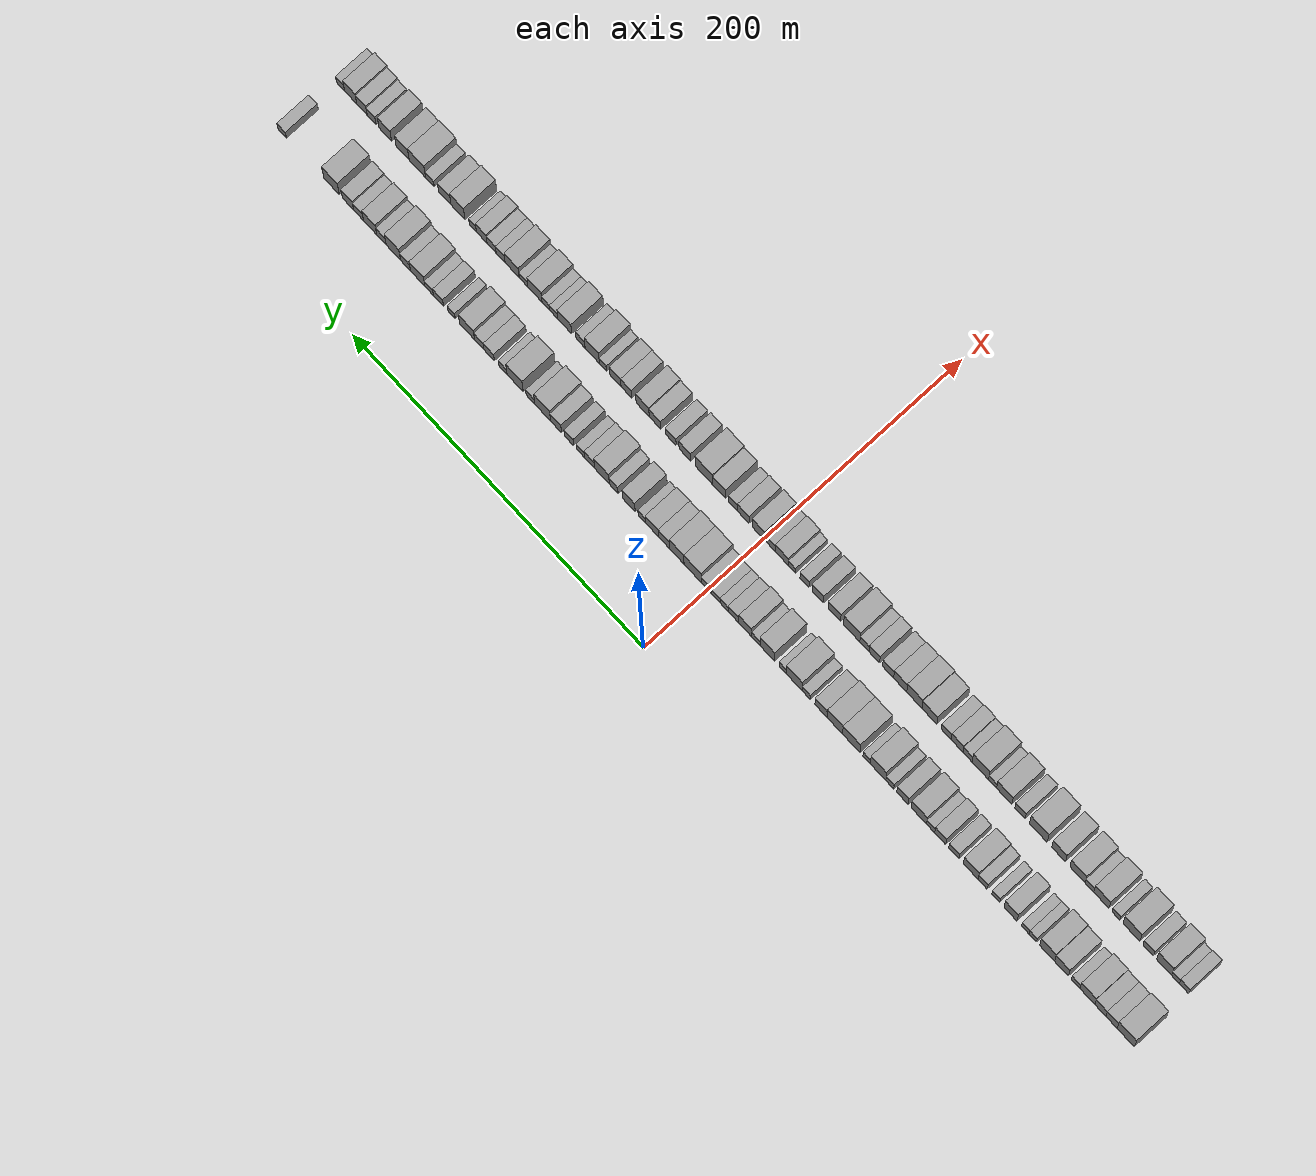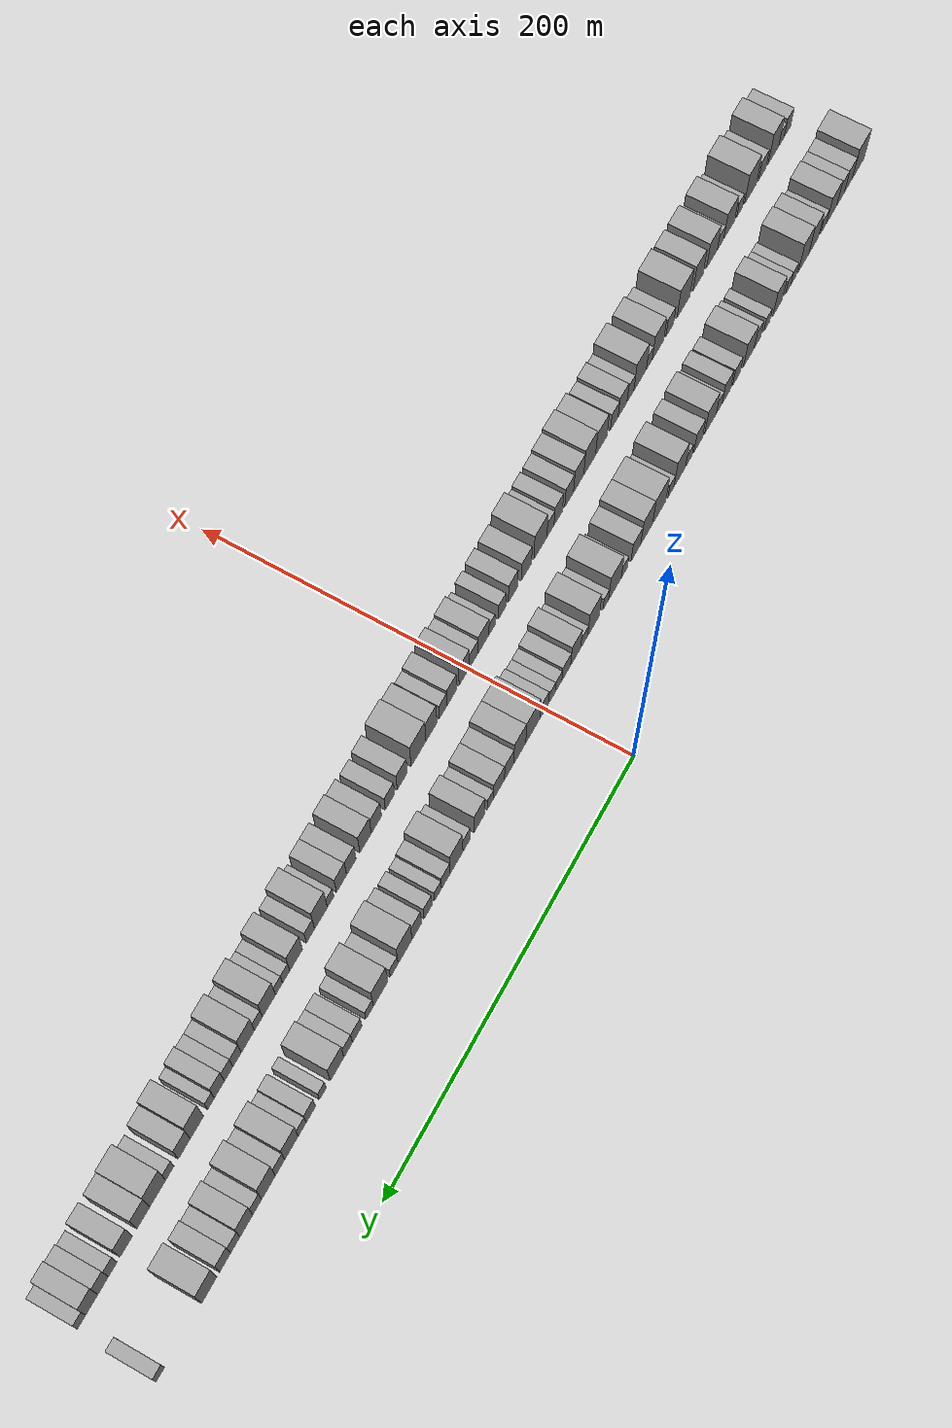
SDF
<sdf version="1.6">
 <world name="default">
  <scene>
   <sky><clouds><speed>12</speed></clouds></sky>
   <ambient>0.4 0.4 0.4 1</ambient>
   <background>0.7 0.7 0.7 1</background>
   <shadows>1</shadows>
  </scene>
  <gravity>0 0 -9.8066</gravity>
  <magnetic_field>6e-06 2.3e-05 -4.2e-05</magnetic_field>
  <physics default="0" name="default_physics" type="ode">
   <ode>
    <solver>
     <type>quick</type>
     <iters>10</iters>
     <sor>1.0</sor>
     <use_dynamic_moi_rescaling>0</use_dynamic_moi_rescaling>
    </solver>
    <constraints>
     <cfm>0</cfm>
     <erp>0.2</erp>
     <contact_max_correcting_vel>100</contact_max_correcting_vel>
     <contact_surface_layer>0.001</contact_surface_layer>
    </constraints>
   </ode>
   <max_step_size>0.004</max_step_size>
   <real_time_factor>1</real_time_factor>
   <real_time_update_rate>250</real_time_update_rate>
  </physics>
  <light name="sun" type="directional">
   <pose>0 0 10 0 0 0</pose>
   <diffuse>0.8 0.8 0.8 1</diffuse>
   <specular>0.2 0.2 0.2 1</specular>
   <attenuation>
    <range>1000</range>
    <constant>0.9</constant>
    <linear>0.01</linear>
    <quadratic>0.001</quadratic>
   </attenuation>
   <direction>-0.5 0.1 -0.9</direction>
  </light>
  <model name="building_1">
   <static>1</static>
   <pose>50.0000 -282.1918 0 0.000000 0.000000 0.000000</pose>
   <link name="link">
    <pose>0 0 12.00 0 0 0</pose>
    <collision name="collision"><geometry><box><size>20.0000 11.6164 24.0000</size></box></geometry></collision>
    <visual name="visual">
     <cast_shadows>0</cast_shadows>
     <geometry><box><size>20.0000 11.6164 24.0000</size></box></geometry>
     <material>
      <script>
       <uri>model://grey_wall/materials/scripts</uri>
       <uri>model://grey_wall/materials/textures</uri>
       <name>vrc/grey_wall</name>
      </script>
     </material>
    </visual>
   </link>
  </model>
  <model name="building_2">
   <static>1</static>
   <pose>50.0000 -272.6289 0 0.000000 0.000000 0.000000</pose>
   <link name="link">
    <pose>0 0 9.00 0 0 0</pose>
    <collision name="collision"><geometry><box><size>20.0000 7.5093 18.0000</size></box></geometry></collision>
    <visual name="visual">
     <cast_shadows>0</cast_shadows>
     <geometry><box><size>20.0000 7.5093 18.0000</size></box></geometry>
     <material>
      <script>
       <uri>model://grey_wall/materials/scripts</uri>
       <uri>model://grey_wall/materials/textures</uri>
       <name>vrc/grey_wall</name>
      </script>
     </material>
    </visual>
   </link>
  </model>
  <model name="building_3">
   <static>1</static>
   <pose>50.0000 -265.1773 0 0.000000 0.000000 0.000000</pose>
   <link name="link">
    <pose>0 0 9.00 0 0 0</pose>
    <collision name="collision"><geometry><box><size>20.0000 7.3941 18.0000</size></box></geometry></collision>
    <visual name="visual">
     <cast_shadows>0</cast_shadows>
     <geometry><box><size>20.0000 7.3941 18.0000</size></box></geometry>
     <material>
      <script>
       <uri>model://grey_wall/materials/scripts</uri>
       <uri>model://grey_wall/materials/textures</uri>
       <name>vrc/grey_wall</name>
      </script>
     </material>
    </visual>
   </link>
  </model>
  <model name="building_4">
   <static>1</static>
   <pose>50.0000 -256.5117 0 0.000000 0.000000 0.000000</pose>
   <link name="link">
    <pose>0 0 10.50 0 0 0</pose>
    <collision name="collision"><geometry><box><size>20.0000 9.9371 21.0000</size></box></geometry></collision>
    <visual name="visual">
     <cast_shadows>0</cast_shadows>
     <geometry><box><size>20.0000 9.9371 21.0000</size></box></geometry>
     <material>
      <script>
       <uri>model://grey_wall/materials/scripts</uri>
       <uri>model://grey_wall/materials/textures</uri>
       <name>vrc/grey_wall</name>
      </script>
     </material>
    </visual>
   </link>
  </model>
  <model name="building_5">
   <static>1</static>
   <pose>50.0000 -248.6620 0 0.000000 0.000000 0.000000</pose>
   <link name="link">
    <pose>0 0 6.00 0 0 0</pose>
    <collision name="collision"><geometry><box><size>20.0000 5.7622 12.0000</size></box></geometry></collision>
    <visual name="visual">
     <cast_shadows>0</cast_shadows>
     <geometry><box><size>20.0000 5.7622 12.0000</size></box></geometry>
     <material>
      <script>
       <uri>model://grey_wall/materials/scripts</uri>
       <uri>model://grey_wall/materials/textures</uri>
       <name>vrc/grey_wall</name>
      </script>
     </material>
    </visual>
   </link>
  </model>
  <model name="building_6">
   <static>1</static>
   <pose>50.0000 -239.1442 0 0.000000 0.000000 0.000000</pose>
   <link name="link">
    <pose>0 0 10.50 0 0 0</pose>
    <collision name="collision"><geometry><box><size>20.0000 9.2733 21.0000</size></box></geometry></collision>
    <visual name="visual">
     <cast_shadows>0</cast_shadows>
     <geometry><box><size>20.0000 9.2733 21.0000</size></box></geometry>
     <material>
      <script>
       <uri>model://grey_wall/materials/scripts</uri>
       <uri>model://grey_wall/materials/textures</uri>
       <name>vrc/grey_wall</name>
      </script>
     </material>
    </visual>
   </link>
  </model>
  <model name="building_7">
   <static>1</static>
   <pose>50.0000 -229.4706 0 0.000000 0.000000 0.000000</pose>
   <link name="link">
    <pose>0 0 12.00 0 0 0</pose>
    <collision name="collision"><geometry><box><size>20.0000 10.0738 24.0000</size></box></geometry></collision>
    <visual name="visual">
     <cast_shadows>0</cast_shadows>
     <geometry><box><size>20.0000 10.0738 24.0000</size></box></geometry>
     <material>
      <script>
       <uri>model://grey_wall/materials/scripts</uri>
       <uri>model://grey_wall/materials/textures</uri>
       <name>vrc/grey_wall</name>
      </script>
     </material>
    </visual>
   </link>
  </model>
  <model name="building_8">
   <static>1</static>
   <pose>50.0000 -219.9659 0 0.000000 0.000000 0.000000</pose>
   <link name="link">
    <pose>0 0 6.00 0 0 0</pose>
    <collision name="collision"><geometry><box><size>20.0000 4.9356 12.0000</size></box></geometry></collision>
    <visual name="visual">
     <cast_shadows>0</cast_shadows>
     <geometry><box><size>20.0000 4.9356 12.0000</size></box></geometry>
     <material>
      <script>
       <uri>model://grey_wall/materials/scripts</uri>
       <uri>model://grey_wall/materials/textures</uri>
       <name>vrc/grey_wall</name>
      </script>
     </material>
    </visual>
   </link>
  </model>
  <model name="building_9">
   <static>1</static>
   <pose>50.0000 -214.8974 0 0.000000 0.000000 0.000000</pose>
   <link name="link">
    <pose>0 0 6.00 0 0 0</pose>
    <collision name="collision"><geometry><box><size>20.0000 5.2013 12.0000</size></box></geometry></collision>
    <visual name="visual">
     <cast_shadows>0</cast_shadows>
     <geometry><box><size>20.0000 5.2013 12.0000</size></box></geometry>
     <material>
      <script>
       <uri>model://grey_wall/materials/scripts</uri>
       <uri>model://grey_wall/materials/textures</uri>
       <name>vrc/grey_wall</name>
      </script>
     </material>
    </visual>
   </link>
  </model>
  <model name="building_10">
   <static>1</static>
   <pose>50.0000 -204.9406 0 0.000000 0.000000 0.000000</pose>
   <link name="link">
    <pose>0 0 10.50 0 0 0</pose>
    <collision name="collision"><geometry><box><size>20.0000 8.7122 21.0000</size></box></geometry></collision>
    <visual name="visual">
     <cast_shadows>0</cast_shadows>
     <geometry><box><size>20.0000 8.7122 21.0000</size></box></geometry>
     <material>
      <script>
       <uri>model://grey_wall/materials/scripts</uri>
       <uri>model://grey_wall/materials/textures</uri>
       <name>vrc/grey_wall</name>
      </script>
     </material>
    </visual>
   </link>
  </model>
  <model name="building_11">
   <static>1</static>
   <pose>50.0000 -194.9367 0 0.000000 0.000000 0.000000</pose>
   <link name="link">
    <pose>0 0 6.00 0 0 0</pose>
    <collision name="collision"><geometry><box><size>20.0000 5.2956 12.0000</size></box></geometry></collision>
    <visual name="visual">
     <cast_shadows>0</cast_shadows>
     <geometry><box><size>20.0000 5.2956 12.0000</size></box></geometry>
     <material>
      <script>
       <uri>model://grey_wall/materials/scripts</uri>
       <uri>model://grey_wall/materials/textures</uri>
       <name>vrc/grey_wall</name>
      </script>
     </material>
    </visual>
   </link>
  </model>
  <model name="building_12">
   <static>1</static>
   <pose>50.0000 -186.1868 0 0.000000 0.000000 0.000000</pose>
   <link name="link">
    <pose>0 0 7.50 0 0 0</pose>
    <collision name="collision"><geometry><box><size>20.0000 6.2042 15.0000</size></box></geometry></collision>
    <visual name="visual">
     <cast_shadows>0</cast_shadows>
     <geometry><box><size>20.0000 6.2042 15.0000</size></box></geometry>
     <material>
      <script>
       <uri>model://grey_wall/materials/scripts</uri>
       <uri>model://grey_wall/materials/textures</uri>
       <name>vrc/grey_wall</name>
      </script>
     </material>
    </visual>
   </link>
  </model>
  <model name="building_13">
   <static>1</static>
   <pose>50.0000 -178.1175 0 0.000000 0.000000 0.000000</pose>
   <link name="link">
    <pose>0 0 10.50 0 0 0</pose>
    <collision name="collision"><geometry><box><size>20.0000 9.9345 21.0000</size></box></geometry></collision>
    <visual name="visual">
     <cast_shadows>0</cast_shadows>
     <geometry><box><size>20.0000 9.9345 21.0000</size></box></geometry>
     <material>
      <script>
       <uri>model://grey_wall/materials/scripts</uri>
       <uri>model://grey_wall/materials/textures</uri>
       <name>vrc/grey_wall</name>
      </script>
     </material>
    </visual>
   </link>
  </model>
  <model name="building_14">
   <static>1</static>
   <pose>50.0000 -166.7029 0 0.000000 0.000000 0.000000</pose>
   <link name="link">
    <pose>0 0 7.50 0 0 0</pose>
    <collision name="collision"><geometry><box><size>20.0000 6.8947 15.0000</size></box></geometry></collision>
    <visual name="visual">
     <cast_shadows>0</cast_shadows>
     <geometry><box><size>20.0000 6.8947 15.0000</size></box></geometry>
     <material>
      <script>
       <uri>model://grey_wall/materials/scripts</uri>
       <uri>model://grey_wall/materials/textures</uri>
       <name>vrc/grey_wall</name>
      </script>
     </material>
    </visual>
   </link>
  </model>
  <model name="building_15">
   <static>1</static>
   <pose>50.0000 -157.5262 0 0.000000 0.000000 0.000000</pose>
   <link name="link">
    <pose>0 0 9.00 0 0 0</pose>
    <collision name="collision"><geometry><box><size>20.0000 7.4588 18.0000</size></box></geometry></collision>
    <visual name="visual">
     <cast_shadows>0</cast_shadows>
     <geometry><box><size>20.0000 7.4588 18.0000</size></box></geometry>
     <material>
      <script>
       <uri>model://grey_wall/materials/scripts</uri>
       <uri>model://grey_wall/materials/textures</uri>
       <name>vrc/grey_wall</name>
      </script>
     </material>
    </visual>
   </link>
  </model>
  <model name="building_16">
   <static>1</static>
   <pose>50.0000 -151.0587 0 0.000000 0.000000 0.000000</pose>
   <link name="link">
    <pose>0 0 6.00 0 0 0</pose>
    <collision name="collision"><geometry><box><size>20.0000 5.4762 12.0000</size></box></geometry></collision>
    <visual name="visual">
     <cast_shadows>0</cast_shadows>
     <geometry><box><size>20.0000 5.4762 12.0000</size></box></geometry>
     <material>
      <script>
       <uri>model://grey_wall/materials/scripts</uri>
       <uri>model://grey_wall/materials/textures</uri>
       <name>vrc/grey_wall</name>
      </script>
     </material>
    </visual>
   </link>
  </model>
  <model name="building_17">
   <static>1</static>
   <pose>50.0000 -143.1364 0 0.000000 0.000000 0.000000</pose>
   <link name="link">
    <pose>0 0 10.50 0 0 0</pose>
    <collision name="collision"><geometry><box><size>20.0000 10.3685 21.0000</size></box></geometry></collision>
    <visual name="visual">
     <cast_shadows>0</cast_shadows>
     <geometry><box><size>20.0000 10.3685 21.0000</size></box></geometry>
     <material>
      <script>
       <uri>model://grey_wall/materials/scripts</uri>
       <uri>model://grey_wall/materials/textures</uri>
       <name>vrc/grey_wall</name>
      </script>
     </material>
    </visual>
   </link>
  </model>
  <model name="building_18">
   <static>1</static>
   <pose>50.0000 -132.0665 0 0.000000 0.000000 0.000000</pose>
   <link name="link">
    <pose>0 0 9.00 0 0 0</pose>
    <collision name="collision"><geometry><box><size>20.0000 7.7713 18.0000</size></box></geometry></collision>
    <visual name="visual">
     <cast_shadows>0</cast_shadows>
     <geometry><box><size>20.0000 7.7713 18.0000</size></box></geometry>
     <material>
      <script>
       <uri>model://grey_wall/materials/scripts</uri>
       <uri>model://grey_wall/materials/textures</uri>
       <name>vrc/grey_wall</name>
      </script>
     </material>
    </visual>
   </link>
  </model>
  <model name="building_19">
   <static>1</static>
   <pose>50.0000 -123.4690 0 0.000000 0.000000 0.000000</pose>
   <link name="link">
    <pose>0 0 6.00 0 0 0</pose>
    <collision name="collision"><geometry><box><size>20.0000 5.4237 12.0000</size></box></geometry></collision>
    <visual name="visual">
     <cast_shadows>0</cast_shadows>
     <geometry><box><size>20.0000 5.4237 12.0000</size></box></geometry>
     <material>
      <script>
       <uri>model://grey_wall/materials/scripts</uri>
       <uri>model://grey_wall/materials/textures</uri>
       <name>vrc/grey_wall</name>
      </script>
     </material>
    </visual>
   </link>
  </model>
  <model name="building_20">
   <static>1</static>
   <pose>50.0000 -115.5682 0 0.000000 0.000000 0.000000</pose>
   <link name="link">
    <pose>0 0 12.00 0 0 0</pose>
    <collision name="collision"><geometry><box><size>20.0000 10.3779 24.0000</size></box></geometry></collision>
    <visual name="visual">
     <cast_shadows>0</cast_shadows>
     <geometry><box><size>20.0000 10.3779 24.0000</size></box></geometry>
     <material>
      <script>
       <uri>model://grey_wall/materials/scripts</uri>
       <uri>model://grey_wall/materials/textures</uri>
       <name>vrc/grey_wall</name>
      </script>
     </material>
    </visual>
   </link>
  </model>
  <model name="building_21">
   <static>1</static>
   <pose>50.0000 -107.8288 0 0.000000 0.000000 0.000000</pose>
   <link name="link">
    <pose>0 0 6.00 0 0 0</pose>
    <collision name="collision"><geometry><box><size>20.0000 5.1009 12.0000</size></box></geometry></collision>
    <visual name="visual">
     <cast_shadows>0</cast_shadows>
     <geometry><box><size>20.0000 5.1009 12.0000</size></box></geometry>
     <material>
      <script>
       <uri>model://grey_wall/materials/scripts</uri>
       <uri>model://grey_wall/materials/textures</uri>
       <name>vrc/grey_wall</name>
      </script>
     </material>
    </visual>
   </link>
  </model>
  <model name="building_22">
   <static>1</static>
   <pose>50.0000 -97.4031 0 0.000000 0.000000 0.000000</pose>
   <link name="link">
    <pose>0 0 12.00 0 0 0</pose>
    <collision name="collision"><geometry><box><size>20.0000 11.7504 24.0000</size></box></geometry></collision>
    <visual name="visual">
     <cast_shadows>0</cast_shadows>
     <geometry><box><size>20.0000 11.7504 24.0000</size></box></geometry>
     <material>
      <script>
       <uri>model://grey_wall/materials/scripts</uri>
       <uri>model://grey_wall/materials/textures</uri>
       <name>vrc/grey_wall</name>
      </script>
     </material>
    </visual>
   </link>
  </model>
  <model name="building_23">
   <static>1</static>
   <pose>50.0000 -86.3627 0 0.000000 0.000000 0.000000</pose>
   <link name="link">
    <pose>0 0 12.00 0 0 0</pose>
    <collision name="collision"><geometry><box><size>20.0000 10.3305 24.0000</size></box></geometry></collision>
    <visual name="visual">
     <cast_shadows>0</cast_shadows>
     <geometry><box><size>20.0000 10.3305 24.0000</size></box></geometry>
     <material>
      <script>
       <uri>model://grey_wall/materials/scripts</uri>
       <uri>model://grey_wall/materials/textures</uri>
       <name>vrc/grey_wall</name>
      </script>
     </material>
    </visual>
   </link>
  </model>
  <model name="building_24">
   <static>1</static>
   <pose>50.0000 -76.9648 0 0.000000 0.000000 0.000000</pose>
   <link name="link">
    <pose>0 0 9.00 0 0 0</pose>
    <collision name="collision"><geometry><box><size>20.0000 8.4652 18.0000</size></box></geometry></collision>
    <visual name="visual">
     <cast_shadows>0</cast_shadows>
     <geometry><box><size>20.0000 8.4652 18.0000</size></box></geometry>
     <material>
      <script>
       <uri>model://grey_wall/materials/scripts</uri>
       <uri>model://grey_wall/materials/textures</uri>
       <name>vrc/grey_wall</name>
      </script>
     </material>
    </visual>
   </link>
  </model>
  <model name="building_25">
   <static>1</static>
   <pose>50.0000 -66.9805 0 0.000000 0.000000 0.000000</pose>
   <link name="link">
    <pose>0 0 6.00 0 0 0</pose>
    <collision name="collision"><geometry><box><size>20.0000 5.5034 12.0000</size></box></geometry></collision>
    <visual name="visual">
     <cast_shadows>0</cast_shadows>
     <geometry><box><size>20.0000 5.5034 12.0000</size></box></geometry>
     <material>
      <script>
       <uri>model://grey_wall/materials/scripts</uri>
       <uri>model://grey_wall/materials/textures</uri>
       <name>vrc/grey_wall</name>
      </script>
     </material>
    </visual>
   </link>
  </model>
  <model name="building_26">
   <static>1</static>
   <pose>50.0000 -58.7749 0 0.000000 0.000000 0.000000</pose>
   <link name="link">
    <pose>0 0 12.00 0 0 0</pose>
    <collision name="collision"><geometry><box><size>20.0000 10.9078 24.0000</size></box></geometry></collision>
    <visual name="visual">
     <cast_shadows>0</cast_shadows>
     <geometry><box><size>20.0000 10.9078 24.0000</size></box></geometry>
     <material>
      <script>
       <uri>model://grey_wall/materials/scripts</uri>
       <uri>model://grey_wall/materials/textures</uri>
       <name>vrc/grey_wall</name>
      </script>
     </material>
    </visual>
   </link>
  </model>
  <model name="building_27">
   <static>1</static>
   <pose>50.0000 -50.8894 0 0.000000 0.000000 0.000000</pose>
   <link name="link">
    <pose>0 0 6.00 0 0 0</pose>
    <collision name="collision"><geometry><box><size>20.0000 4.8633 12.0000</size></box></geometry></collision>
    <visual name="visual">
     <cast_shadows>0</cast_shadows>
     <geometry><box><size>20.0000 4.8633 12.0000</size></box></geometry>
     <material>
      <script>
       <uri>model://grey_wall/materials/scripts</uri>
       <uri>model://grey_wall/materials/textures</uri>
       <name>vrc/grey_wall</name>
      </script>
     </material>
    </visual>
   </link>
  </model>
  <model name="building_28">
   <static>1</static>
   <pose>50.0000 -40.4735 0 0.000000 0.000000 0.000000</pose>
   <link name="link">
    <pose>0 0 12.00 0 0 0</pose>
    <collision name="collision"><geometry><box><size>20.0000 9.9685 24.0000</size></box></geometry></collision>
    <visual name="visual">
     <cast_shadows>0</cast_shadows>
     <geometry><box><size>20.0000 9.9685 24.0000</size></box></geometry>
     <material>
      <script>
       <uri>model://grey_wall/materials/scripts</uri>
       <uri>model://grey_wall/materials/textures</uri>
       <name>vrc/grey_wall</name>
      </script>
     </material>
    </visual>
   </link>
  </model>
  <model name="building_29">
   <static>1</static>
   <pose>50.0000 -32.5656 0 0.000000 0.000000 0.000000</pose>
   <link name="link">
    <pose>0 0 6.00 0 0 0</pose>
    <collision name="collision"><geometry><box><size>20.0000 5.8473 12.0000</size></box></geometry></collision>
    <visual name="visual">
     <cast_shadows>0</cast_shadows>
     <geometry><box><size>20.0000 5.8473 12.0000</size></box></geometry>
     <material>
      <script>
       <uri>model://grey_wall/materials/scripts</uri>
       <uri>model://grey_wall/materials/textures</uri>
       <name>vrc/grey_wall</name>
      </script>
     </material>
    </visual>
   </link>
  </model>
  <model name="building_30">
   <static>1</static>
   <pose>50.0000 -25.3469 0 0.000000 0.000000 0.000000</pose>
   <link name="link">
    <pose>0 0 10.50 0 0 0</pose>
    <collision name="collision"><geometry><box><size>20.0000 8.5902 21.0000</size></box></geometry></collision>
    <visual name="visual">
     <cast_shadows>0</cast_shadows>
     <geometry><box><size>20.0000 8.5902 21.0000</size></box></geometry>
     <material>
      <script>
       <uri>model://grey_wall/materials/scripts</uri>
       <uri>model://grey_wall/materials/textures</uri>
       <name>vrc/grey_wall</name>
      </script>
     </material>
    </visual>
   </link>
  </model>
  <model name="building_31">
   <static>1</static>
   <pose>50.0000 -17.3858 0 0.000000 0.000000 0.000000</pose>
   <link name="link">
    <pose>0 0 7.50 0 0 0</pose>
    <collision name="collision"><geometry><box><size>20.0000 7.3321 15.0000</size></box></geometry></collision>
    <visual name="visual">
     <cast_shadows>0</cast_shadows>
     <geometry><box><size>20.0000 7.3321 15.0000</size></box></geometry>
     <material>
      <script>
       <uri>model://grey_wall/materials/scripts</uri>
       <uri>model://grey_wall/materials/textures</uri>
       <name>vrc/grey_wall</name>
      </script>
     </material>
    </visual>
   </link>
  </model>
  <model name="building_32">
   <static>1</static>
   <pose>50.0000 -10.9680 0 0.000000 0.000000 0.000000</pose>
   <link name="link">
    <pose>0 0 6.00 0 0 0</pose>
    <collision name="collision"><geometry><box><size>20.0000 5.5035 12.0000</size></box></geometry></collision>
    <visual name="visual">
     <cast_shadows>0</cast_shadows>
     <geometry><box><size>20.0000 5.5035 12.0000</size></box></geometry>
     <material>
      <script>
       <uri>model://grey_wall/materials/scripts</uri>
       <uri>model://grey_wall/materials/textures</uri>
       <name>vrc/grey_wall</name>
      </script>
     </material>
    </visual>
   </link>
  </model>
  <model name="building_33">
   <static>1</static>
   <pose>50.0000 -5.3943 0 0.000000 0.000000 0.000000</pose>
   <link name="link">
    <pose>0 0 6.00 0 0 0</pose>
    <collision name="collision"><geometry><box><size>20.0000 5.6439 12.0000</size></box></geometry></collision>
    <visual name="visual">
     <cast_shadows>0</cast_shadows>
     <geometry><box><size>20.0000 5.6439 12.0000</size></box></geometry>
     <material>
      <script>
       <uri>model://grey_wall/materials/scripts</uri>
       <uri>model://grey_wall/materials/textures</uri>
       <name>vrc/grey_wall</name>
      </script>
     </material>
    </visual>
   </link>
  </model>
  <model name="building_34">
   <static>1</static>
   <pose>50.0000 0.9988 0 0.000000 0.000000 0.000000</pose>
   <link name="link">
    <pose>0 0 7.50 0 0 0</pose>
    <collision name="collision"><geometry><box><size>20.0000 7.1422 15.0000</size></box></geometry></collision>
    <visual name="visual">
     <cast_shadows>0</cast_shadows>
     <geometry><box><size>20.0000 7.1422 15.0000</size></box></geometry>
     <material>
      <script>
       <uri>model://grey_wall/materials/scripts</uri>
       <uri>model://grey_wall/materials/textures</uri>
       <name>vrc/grey_wall</name>
      </script>
     </material>
    </visual>
   </link>
  </model>
  <model name="building_35">
   <static>1</static>
   <pose>50.0000 10.4625 0 0.000000 0.000000 0.000000</pose>
   <link name="link">
    <pose>0 0 12.00 0 0 0</pose>
    <collision name="collision"><geometry><box><size>20.0000 11.7853 24.0000</size></box></geometry></collision>
    <visual name="visual">
     <cast_shadows>0</cast_shadows>
     <geometry><box><size>20.0000 11.7853 24.0000</size></box></geometry>
     <material>
      <script>
       <uri>model://grey_wall/materials/scripts</uri>
       <uri>model://grey_wall/materials/textures</uri>
       <name>vrc/grey_wall</name>
      </script>
     </material>
    </visual>
   </link>
  </model>
  <model name="building_36">
   <static>1</static>
   <pose>50.0000 21.2735 0 0.000000 0.000000 0.000000</pose>
   <link name="link">
    <pose>0 0 12.00 0 0 0</pose>
    <collision name="collision"><geometry><box><size>20.0000 9.8368 24.0000</size></box></geometry></collision>
    <visual name="visual">
     <cast_shadows>0</cast_shadows>
     <geometry><box><size>20.0000 9.8368 24.0000</size></box></geometry>
     <material>
      <script>
       <uri>model://grey_wall/materials/scripts</uri>
       <uri>model://grey_wall/materials/textures</uri>
       <name>vrc/grey_wall</name>
      </script>
     </material>
    </visual>
   </link>
  </model>
  <model name="building_37">
   <static>1</static>
   <pose>50.0000 30.0044 0 0.000000 0.000000 0.000000</pose>
   <link name="link">
    <pose>0 0 9.00 0 0 0</pose>
    <collision name="collision"><geometry><box><size>20.0000 7.6249 18.0000</size></box></geometry></collision>
    <visual name="visual">
     <cast_shadows>0</cast_shadows>
     <geometry><box><size>20.0000 7.6249 18.0000</size></box></geometry>
     <material>
      <script>
       <uri>model://grey_wall/materials/scripts</uri>
       <uri>model://grey_wall/materials/textures</uri>
       <name>vrc/grey_wall</name>
      </script>
     </material>
    </visual>
   </link>
  </model>
  <model name="building_38">
   <static>1</static>
   <pose>50.0000 38.2437 0 0.000000 0.000000 0.000000</pose>
   <link name="link">
    <pose>0 0 9.00 0 0 0</pose>
    <collision name="collision"><geometry><box><size>20.0000 8.8538 18.0000</size></box></geometry></collision>
    <visual name="visual">
     <cast_shadows>0</cast_shadows>
     <geometry><box><size>20.0000 8.8538 18.0000</size></box></geometry>
     <material>
      <script>
       <uri>model://grey_wall/materials/scripts</uri>
       <uri>model://grey_wall/materials/textures</uri>
       <name>vrc/grey_wall</name>
      </script>
     </material>
    </visual>
   </link>
  </model>
  <model name="building_39">
   <static>1</static>
   <pose>50.0000 45.1962 0 0.000000 0.000000 0.000000</pose>
   <link name="link">
    <pose>0 0 6.00 0 0 0</pose>
    <collision name="collision"><geometry><box><size>20.0000 5.0511 12.0000</size></box></geometry></collision>
    <visual name="visual">
     <cast_shadows>0</cast_shadows>
     <geometry><box><size>20.0000 5.0511 12.0000</size></box></geometry>
     <material>
      <script>
       <uri>model://grey_wall/materials/scripts</uri>
       <uri>model://grey_wall/materials/textures</uri>
       <name>vrc/grey_wall</name>
      </script>
     </material>
    </visual>
   </link>
  </model>
  <model name="building_40">
   <static>1</static>
   <pose>50.0000 54.0515 0 0.000000 0.000000 0.000000</pose>
   <link name="link">
    <pose>0 0 10.50 0 0 0</pose>
    <collision name="collision"><geometry><box><size>20.0000 8.6596 21.0000</size></box></geometry></collision>
    <visual name="visual">
     <cast_shadows>0</cast_shadows>
     <geometry><box><size>20.0000 8.6596 21.0000</size></box></geometry>
     <material>
      <script>
       <uri>model://grey_wall/materials/scripts</uri>
       <uri>model://grey_wall/materials/textures</uri>
       <name>vrc/grey_wall</name>
      </script>
     </material>
    </visual>
   </link>
  </model>
  <model name="building_41">
   <static>1</static>
   <pose>50.0000 64.3999 0 0.000000 0.000000 0.000000</pose>
   <link name="link">
    <pose>0 0 7.50 0 0 0</pose>
    <collision name="collision"><geometry><box><size>20.0000 6.0371 15.0000</size></box></geometry></collision>
    <visual name="visual">
     <cast_shadows>0</cast_shadows>
     <geometry><box><size>20.0000 6.0371 15.0000</size></box></geometry>
     <material>
      <script>
       <uri>model://grey_wall/materials/scripts</uri>
       <uri>model://grey_wall/materials/textures</uri>
       <name>vrc/grey_wall</name>
      </script>
     </material>
    </visual>
   </link>
  </model>
  <model name="building_42">
   <static>1</static>
   <pose>50.0000 72.4679 0 0.000000 0.000000 0.000000</pose>
   <link name="link">
    <pose>0 0 12.00 0 0 0</pose>
    <collision name="collision"><geometry><box><size>20.0000 10.0989 24.0000</size></box></geometry></collision>
    <visual name="visual">
     <cast_shadows>0</cast_shadows>
     <geometry><box><size>20.0000 10.0989 24.0000</size></box></geometry>
     <material>
      <script>
       <uri>model://grey_wall/materials/scripts</uri>
       <uri>model://grey_wall/materials/textures</uri>
       <name>vrc/grey_wall</name>
      </script>
     </material>
    </visual>
   </link>
  </model>
  <model name="building_43">
   <static>1</static>
   <pose>50.0000 80.9855 0 0.000000 0.000000 0.000000</pose>
   <link name="link">
    <pose>0 0 7.50 0 0 0</pose>
    <collision name="collision"><geometry><box><size>20.0000 6.9362 15.0000</size></box></geometry></collision>
    <visual name="visual">
     <cast_shadows>0</cast_shadows>
     <geometry><box><size>20.0000 6.9362 15.0000</size></box></geometry>
     <material>
      <script>
       <uri>model://grey_wall/materials/scripts</uri>
       <uri>model://grey_wall/materials/textures</uri>
       <name>vrc/grey_wall</name>
      </script>
     </material>
    </visual>
   </link>
  </model>
  <model name="building_44">
   <static>1</static>
   <pose>50.0000 87.1858 0 0.000000 0.000000 0.000000</pose>
   <link name="link">
    <pose>0 0 6.00 0 0 0</pose>
    <collision name="collision"><geometry><box><size>20.0000 5.4644 12.0000</size></box></geometry></collision>
    <visual name="visual">
     <cast_shadows>0</cast_shadows>
     <geometry><box><size>20.0000 5.4644 12.0000</size></box></geometry>
     <material>
      <script>
       <uri>model://grey_wall/materials/scripts</uri>
       <uri>model://grey_wall/materials/textures</uri>
       <name>vrc/grey_wall</name>
      </script>
     </material>
    </visual>
   </link>
  </model>
  <model name="building_45">
   <static>1</static>
   <pose>50.0000 95.0494 0 0.000000 0.000000 0.000000</pose>
   <link name="link">
    <pose>0 0 7.50 0 0 0</pose>
    <collision name="collision"><geometry><box><size>20.0000 6.2626 15.0000</size></box></geometry></collision>
    <visual name="visual">
     <cast_shadows>0</cast_shadows>
     <geometry><box><size>20.0000 6.2626 15.0000</size></box></geometry>
     <material>
      <script>
       <uri>model://grey_wall/materials/scripts</uri>
       <uri>model://grey_wall/materials/textures</uri>
       <name>vrc/grey_wall</name>
      </script>
     </material>
    </visual>
   </link>
  </model>
  <model name="building_46">
   <static>1</static>
   <pose>50.0000 103.9165 0 0.000000 0.000000 0.000000</pose>
   <link name="link">
    <pose>0 0 9.00 0 0 0</pose>
    <collision name="collision"><geometry><box><size>20.0000 7.4715 18.0000</size></box></geometry></collision>
    <visual name="visual">
     <cast_shadows>0</cast_shadows>
     <geometry><box><size>20.0000 7.4715 18.0000</size></box></geometry>
     <material>
      <script>
       <uri>model://grey_wall/materials/scripts</uri>
       <uri>model://grey_wall/materials/textures</uri>
       <name>vrc/grey_wall</name>
      </script>
     </material>
    </visual>
   </link>
  </model>
  <model name="building_47">
   <static>1</static>
   <pose>50.0000 113.0806 0 0.000000 0.000000 0.000000</pose>
   <link name="link">
    <pose>0 0 12.00 0 0 0</pose>
    <collision name="collision"><geometry><box><size>20.0000 10.8569 24.0000</size></box></geometry></collision>
    <visual name="visual">
     <cast_shadows>0</cast_shadows>
     <geometry><box><size>20.0000 10.8569 24.0000</size></box></geometry>
     <material>
      <script>
       <uri>model://grey_wall/materials/scripts</uri>
       <uri>model://grey_wall/materials/textures</uri>
       <name>vrc/grey_wall</name>
      </script>
     </material>
    </visual>
   </link>
  </model>
  <model name="building_48">
   <static>1</static>
   <pose>50.0000 121.5060 0 0.000000 0.000000 0.000000</pose>
   <link name="link">
    <pose>0 0 6.00 0 0 0</pose>
    <collision name="collision"><geometry><box><size>20.0000 5.9939 12.0000</size></box></geometry></collision>
    <visual name="visual">
     <cast_shadows>0</cast_shadows>
     <geometry><box><size>20.0000 5.9939 12.0000</size></box></geometry>
     <material>
      <script>
       <uri>model://grey_wall/materials/scripts</uri>
       <uri>model://grey_wall/materials/textures</uri>
       <name>vrc/grey_wall</name>
      </script>
     </material>
    </visual>
   </link>
  </model>
  <model name="building_49">
   <static>1</static>
   <pose>50.0000 132.0567 0 0.000000 0.000000 0.000000</pose>
   <link name="link">
    <pose>0 0 12.00 0 0 0</pose>
    <collision name="collision"><geometry><box><size>20.0000 11.1073 24.0000</size></box></geometry></collision>
    <visual name="visual">
     <cast_shadows>0</cast_shadows>
     <geometry><box><size>20.0000 11.1073 24.0000</size></box></geometry>
     <material>
      <script>
       <uri>model://grey_wall/materials/scripts</uri>
       <uri>model://grey_wall/materials/textures</uri>
       <name>vrc/grey_wall</name>
      </script>
     </material>
    </visual>
   </link>
  </model>
  <model name="building_50">
   <static>1</static>
   <pose>50.0000 140.4432 0 0.000000 0.000000 0.000000</pose>
   <link name="link">
    <pose>0 0 6.00 0 0 0</pose>
    <collision name="collision"><geometry><box><size>20.0000 5.6658 12.0000</size></box></geometry></collision>
    <visual name="visual">
     <cast_shadows>0</cast_shadows>
     <geometry><box><size>20.0000 5.6658 12.0000</size></box></geometry>
     <material>
      <script>
       <uri>model://grey_wall/materials/scripts</uri>
       <uri>model://grey_wall/materials/textures</uri>
       <name>vrc/grey_wall</name>
      </script>
     </material>
    </visual>
   </link>
  </model>
  <model name="building_51">
   <static>1</static>
   <pose>50.0000 149.8587 0 0.000000 0.000000 0.000000</pose>
   <link name="link">
    <pose>0 0 7.50 0 0 0</pose>
    <collision name="collision"><geometry><box><size>20.0000 7.1651 15.0000</size></box></geometry></collision>
    <visual name="visual">
     <cast_shadows>0</cast_shadows>
     <geometry><box><size>20.0000 7.1651 15.0000</size></box></geometry>
     <material>
      <script>
       <uri>model://grey_wall/materials/scripts</uri>
       <uri>model://grey_wall/materials/textures</uri>
       <name>vrc/grey_wall</name>
      </script>
     </material>
    </visual>
   </link>
  </model>
  <model name="building_52">
   <static>1</static>
   <pose>50.0000 156.7073 0 0.000000 0.000000 0.000000</pose>
   <link name="link">
    <pose>0 0 7.50 0 0 0</pose>
    <collision name="collision"><geometry><box><size>20.0000 6.5321 15.0000</size></box></geometry></collision>
    <visual name="visual">
     <cast_shadows>0</cast_shadows>
     <geometry><box><size>20.0000 6.5321 15.0000</size></box></geometry>
     <material>
      <script>
       <uri>model://grey_wall/materials/scripts</uri>
       <uri>model://grey_wall/materials/textures</uri>
       <name>vrc/grey_wall</name>
      </script>
     </material>
    </visual>
   </link>
  </model>
  <model name="building_53">
   <static>1</static>
   <pose>50.0000 165.1053 0 0.000000 0.000000 0.000000</pose>
   <link name="link">
    <pose>0 0 10.50 0 0 0</pose>
    <collision name="collision"><geometry><box><size>20.0000 10.2638 21.0000</size></box></geometry></collision>
    <visual name="visual">
     <cast_shadows>0</cast_shadows>
     <geometry><box><size>20.0000 10.2638 21.0000</size></box></geometry>
     <material>
      <script>
       <uri>model://grey_wall/materials/scripts</uri>
       <uri>model://grey_wall/materials/textures</uri>
       <name>vrc/grey_wall</name>
      </script>
     </material>
    </visual>
   </link>
  </model>
  <model name="building_54">
   <static>1</static>
   <pose>50.0000 175.7789 0 0.000000 0.000000 0.000000</pose>
   <link name="link">
    <pose>0 0 6.00 0 0 0</pose>
    <collision name="collision"><geometry><box><size>20.0000 5.0835 12.0000</size></box></geometry></collision>
    <visual name="visual">
     <cast_shadows>0</cast_shadows>
     <geometry><box><size>20.0000 5.0835 12.0000</size></box></geometry>
     <material>
      <script>
       <uri>model://grey_wall/materials/scripts</uri>
       <uri>model://grey_wall/materials/textures</uri>
       <name>vrc/grey_wall</name>
      </script>
     </material>
    </visual>
   </link>
  </model>
  <model name="building_55">
   <static>1</static>
   <pose>50.0000 184.7896 0 0.000000 0.000000 0.000000</pose>
   <link name="link">
    <pose>0 0 7.50 0 0 0</pose>
    <collision name="collision"><geometry><box><size>20.0000 6.9380 15.0000</size></box></geometry></collision>
    <visual name="visual">
     <cast_shadows>0</cast_shadows>
     <geometry><box><size>20.0000 6.9380 15.0000</size></box></geometry>
     <material>
      <script>
       <uri>model://grey_wall/materials/scripts</uri>
       <uri>model://grey_wall/materials/textures</uri>
       <name>vrc/grey_wall</name>
      </script>
     </material>
    </visual>
   </link>
  </model>
  <model name="building_56">
   <static>1</static>
   <pose>50.0000 191.2132 0 0.000000 0.000000 0.000000</pose>
   <link name="link">
    <pose>0 0 6.00 0 0 0</pose>
    <collision name="collision"><geometry><box><size>20.0000 5.9091 12.0000</size></box></geometry></collision>
    <visual name="visual">
     <cast_shadows>0</cast_shadows>
     <geometry><box><size>20.0000 5.9091 12.0000</size></box></geometry>
     <material>
      <script>
       <uri>model://grey_wall/materials/scripts</uri>
       <uri>model://grey_wall/materials/textures</uri>
       <name>vrc/grey_wall</name>
      </script>
     </material>
    </visual>
   </link>
  </model>
  <model name="building_57">
   <static>1</static>
   <pose>50.0000 199.1576 0 0.000000 0.000000 0.000000</pose>
   <link name="link">
    <pose>0 0 10.50 0 0 0</pose>
    <collision name="collision"><geometry><box><size>20.0000 9.9797 21.0000</size></box></geometry></collision>
    <visual name="visual">
     <cast_shadows>0</cast_shadows>
     <geometry><box><size>20.0000 9.9797 21.0000</size></box></geometry>
     <material>
      <script>
       <uri>model://grey_wall/materials/scripts</uri>
       <uri>model://grey_wall/materials/textures</uri>
       <name>vrc/grey_wall</name>
      </script>
     </material>
    </visual>
   </link>
  </model>
  <model name="building_58">
   <static>1</static>
   <pose>50.0000 207.5786 0 0.000000 0.000000 0.000000</pose>
   <link name="link">
    <pose>0 0 7.50 0 0 0</pose>
    <collision name="collision"><geometry><box><size>20.0000 6.8624 15.0000</size></box></geometry></collision>
    <visual name="visual">
     <cast_shadows>0</cast_shadows>
     <geometry><box><size>20.0000 6.8624 15.0000</size></box></geometry>
     <material>
      <script>
       <uri>model://grey_wall/materials/scripts</uri>
       <uri>model://grey_wall/materials/textures</uri>
       <name>vrc/grey_wall</name>
      </script>
     </material>
    </visual>
   </link>
  </model>
  <model name="building_59">
   <static>1</static>
   <pose>50.0000 215.9971 0 0.000000 0.000000 0.000000</pose>
   <link name="link">
    <pose>0 0 12.00 0 0 0</pose>
    <collision name="collision"><geometry><box><size>20.0000 9.9745 24.0000</size></box></geometry></collision>
    <visual name="visual">
     <cast_shadows>0</cast_shadows>
     <geometry><box><size>20.0000 9.9745 24.0000</size></box></geometry>
     <material>
      <script>
       <uri>model://grey_wall/materials/scripts</uri>
       <uri>model://grey_wall/materials/textures</uri>
       <name>vrc/grey_wall</name>
      </script>
     </material>
    </visual>
   </link>
  </model>
  <model name="building_60">
   <static>1</static>
   <pose>50.0000 224.2173 0 0.000000 0.000000 0.000000</pose>
   <link name="link">
    <pose>0 0 7.50 0 0 0</pose>
    <collision name="collision"><geometry><box><size>20.0000 6.4659 15.0000</size></box></geometry></collision>
    <visual name="visual">
     <cast_shadows>0</cast_shadows>
     <geometry><box><size>20.0000 6.4659 15.0000</size></box></geometry>
     <material>
      <script>
       <uri>model://grey_wall/materials/scripts</uri>
       <uri>model://grey_wall/materials/textures</uri>
       <name>vrc/grey_wall</name>
      </script>
     </material>
    </visual>
   </link>
  </model>
  <model name="building_61">
   <static>1</static>
   <pose>50.0000 232.0735 0 0.000000 0.000000 0.000000</pose>
   <link name="link">
    <pose>0 0 10.50 0 0 0</pose>
    <collision name="collision"><geometry><box><size>20.0000 9.2464 21.0000</size></box></geometry></collision>
    <visual name="visual">
     <cast_shadows>0</cast_shadows>
     <geometry><box><size>20.0000 9.2464 21.0000</size></box></geometry>
     <material>
      <script>
       <uri>model://grey_wall/materials/scripts</uri>
       <uri>model://grey_wall/materials/textures</uri>
       <name>vrc/grey_wall</name>
      </script>
     </material>
    </visual>
   </link>
  </model>
  <model name="building_62">
   <static>1</static>
   <pose>50.0000 240.0651 0 0.000000 0.000000 0.000000</pose>
   <link name="link">
    <pose>0 0 7.50 0 0 0</pose>
    <collision name="collision"><geometry><box><size>20.0000 6.7368 15.0000</size></box></geometry></collision>
    <visual name="visual">
     <cast_shadows>0</cast_shadows>
     <geometry><box><size>20.0000 6.7368 15.0000</size></box></geometry>
     <material>
      <script>
       <uri>model://grey_wall/materials/scripts</uri>
       <uri>model://grey_wall/materials/textures</uri>
       <name>vrc/grey_wall</name>
      </script>
     </material>
    </visual>
   </link>
  </model>
  <model name="building_63">
   <static>1</static>
   <pose>50.0000 247.3832 0 0.000000 0.000000 0.000000</pose>
   <link name="link">
    <pose>0 0 9.00 0 0 0</pose>
    <collision name="collision"><geometry><box><size>20.0000 7.8994 18.0000</size></box></geometry></collision>
    <visual name="visual">
     <cast_shadows>0</cast_shadows>
     <geometry><box><size>20.0000 7.8994 18.0000</size></box></geometry>
     <material>
      <script>
       <uri>model://grey_wall/materials/scripts</uri>
       <uri>model://grey_wall/materials/textures</uri>
       <name>vrc/grey_wall</name>
      </script>
     </material>
    </visual>
   </link>
  </model>
  <model name="building_64">
   <static>1</static>
   <pose>50.0000 258.7395 0 0.000000 0.000000 0.000000</pose>
   <link name="link">
    <pose>0 0 12.00 0 0 0</pose>
    <collision name="collision"><geometry><box><size>20.0000 10.8131 24.0000</size></box></geometry></collision>
    <visual name="visual">
     <cast_shadows>0</cast_shadows>
     <geometry><box><size>20.0000 10.8131 24.0000</size></box></geometry>
     <material>
      <script>
       <uri>model://grey_wall/materials/scripts</uri>
       <uri>model://grey_wall/materials/textures</uri>
       <name>vrc/grey_wall</name>
      </script>
     </material>
    </visual>
   </link>
  </model>
  <model name="building_65">
   <static>1</static>
   <pose>50.0000 293.0234 0 0.000000 0.000000 0.000000</pose>
   <link name="link">
    <pose>0 0 6.00 0 0 0</pose>
    <collision name="collision"><geometry><box><size>20.0000 5.9182 12.0000</size></box></geometry></collision>
    <visual name="visual">
     <cast_shadows>0</cast_shadows>
     <geometry><box><size>20.0000 5.9182 12.0000</size></box></geometry>
     <material>
      <script>
       <uri>model://grey_wall/materials/scripts</uri>
       <uri>model://grey_wall/materials/textures</uri>
       <name>vrc/grey_wall</name>
      </script>
     </material>
    </visual>
   </link>
  </model>
  <model name="building_66">
   <static>1</static>
   <pose>85.0000 -283.8092 0 0.000000 0.000000 0.000000</pose>
   <link name="link">
    <pose>0 0 7.50 0 0 0</pose>
    <collision name="collision"><geometry><box><size>20.0000 6.3816 15.0000</size></box></geometry></collision>
    <visual name="visual">
     <cast_shadows>0</cast_shadows>
     <geometry><box><size>20.0000 6.3816 15.0000</size></box></geometry>
     <material>
      <script>
       <uri>model://grey_wall/materials/scripts</uri>
       <uri>model://grey_wall/materials/textures</uri>
       <name>vrc/grey_wall</name>
      </script>
     </material>
    </visual>
   </link>
  </model>
  <model name="building_67">
   <static>1</static>
   <pose>85.0000 -277.9953 0 0.000000 0.000000 0.000000</pose>
   <link name="link">
    <pose>0 0 6.00 0 0 0</pose>
    <collision name="collision"><geometry><box><size>20.0000 5.2462 12.0000</size></box></geometry></collision>
    <visual name="visual">
     <cast_shadows>0</cast_shadows>
     <geometry><box><size>20.0000 5.2462 12.0000</size></box></geometry>
     <material>
      <script>
       <uri>model://grey_wall/materials/scripts</uri>
       <uri>model://grey_wall/materials/textures</uri>
       <name>vrc/grey_wall</name>
      </script>
     </material>
    </visual>
   </link>
  </model>
  <model name="building_68">
   <static>1</static>
   <pose>85.0000 -270.3842 0 0.000000 0.000000 0.000000</pose>
   <link name="link">
    <pose>0 0 12.00 0 0 0</pose>
    <collision name="collision"><geometry><box><size>20.0000 9.9761 24.0000</size></box></geometry></collision>
    <visual name="visual">
     <cast_shadows>0</cast_shadows>
     <geometry><box><size>20.0000 9.9761 24.0000</size></box></geometry>
     <material>
      <script>
       <uri>model://grey_wall/materials/scripts</uri>
       <uri>model://grey_wall/materials/textures</uri>
       <name>vrc/grey_wall</name>
      </script>
     </material>
    </visual>
   </link>
  </model>
  <model name="building_69">
   <static>1</static>
   <pose>85.0000 -259.8183 0 0.000000 0.000000 0.000000</pose>
   <link name="link">
    <pose>0 0 7.50 0 0 0</pose>
    <collision name="collision"><geometry><box><size>20.0000 7.1557 15.0000</size></box></geometry></collision>
    <visual name="visual">
     <cast_shadows>0</cast_shadows>
     <geometry><box><size>20.0000 7.1557 15.0000</size></box></geometry>
     <material>
      <script>
       <uri>model://grey_wall/materials/scripts</uri>
       <uri>model://grey_wall/materials/textures</uri>
       <name>vrc/grey_wall</name>
      </script>
     </material>
    </visual>
   </link>
  </model>
  <model name="building_70">
   <static>1</static>
   <pose>85.0000 -248.5477 0 0.000000 0.000000 0.000000</pose>
   <link name="link">
    <pose>0 0 12.00 0 0 0</pose>
    <collision name="collision"><geometry><box><size>20.0000 11.3855 24.0000</size></box></geometry></collision>
    <visual name="visual">
     <cast_shadows>0</cast_shadows>
     <geometry><box><size>20.0000 11.3855 24.0000</size></box></geometry>
     <material>
      <script>
       <uri>model://grey_wall/materials/scripts</uri>
       <uri>model://grey_wall/materials/textures</uri>
       <name>vrc/grey_wall</name>
      </script>
     </material>
    </visual>
   </link>
  </model>
  <model name="building_71">
   <static>1</static>
   <pose>85.0000 -238.1983 0 0.000000 0.000000 0.000000</pose>
   <link name="link">
    <pose>0 0 6.00 0 0 0</pose>
    <collision name="collision"><geometry><box><size>20.0000 5.3133 12.0000</size></box></geometry></collision>
    <visual name="visual">
     <cast_shadows>0</cast_shadows>
     <geometry><box><size>20.0000 5.3133 12.0000</size></box></geometry>
     <material>
      <script>
       <uri>model://grey_wall/materials/scripts</uri>
       <uri>model://grey_wall/materials/textures</uri>
       <name>vrc/grey_wall</name>
      </script>
     </material>
    </visual>
   </link>
  </model>
  <model name="building_72">
   <static>1</static>
   <pose>85.0000 -228.4284 0 0.000000 0.000000 0.000000</pose>
   <link name="link">
    <pose>0 0 10.50 0 0 0</pose>
    <collision name="collision"><geometry><box><size>20.0000 10.2266 21.0000</size></box></geometry></collision>
    <visual name="visual">
     <cast_shadows>0</cast_shadows>
     <geometry><box><size>20.0000 10.2266 21.0000</size></box></geometry>
     <material>
      <script>
       <uri>model://grey_wall/materials/scripts</uri>
       <uri>model://grey_wall/materials/textures</uri>
       <name>vrc/grey_wall</name>
      </script>
     </material>
    </visual>
   </link>
  </model>
  <model name="building_73">
   <static>1</static>
   <pose>85.0000 -220.3913 0 0.000000 0.000000 0.000000</pose>
   <link name="link">
    <pose>0 0 6.00 0 0 0</pose>
    <collision name="collision"><geometry><box><size>20.0000 5.8476 12.0000</size></box></geometry></collision>
    <visual name="visual">
     <cast_shadows>0</cast_shadows>
     <geometry><box><size>20.0000 5.8476 12.0000</size></box></geometry>
     <material>
      <script>
       <uri>model://grey_wall/materials/scripts</uri>
       <uri>model://grey_wall/materials/textures</uri>
       <name>vrc/grey_wall</name>
      </script>
     </material>
    </visual>
   </link>
  </model>
  <model name="building_74">
   <static>1</static>
   <pose>85.0000 -212.3666 0 0.000000 0.000000 0.000000</pose>
   <link name="link">
    <pose>0 0 10.50 0 0 0</pose>
    <collision name="collision"><geometry><box><size>20.0000 10.2017 21.0000</size></box></geometry></collision>
    <visual name="visual">
     <cast_shadows>0</cast_shadows>
     <geometry><box><size>20.0000 10.2017 21.0000</size></box></geometry>
     <material>
      <script>
       <uri>model://grey_wall/materials/scripts</uri>
       <uri>model://grey_wall/materials/textures</uri>
       <name>vrc/grey_wall</name>
      </script>
     </material>
    </visual>
   </link>
  </model>
  <model name="building_75">
   <static>1</static>
   <pose>85.0000 -199.6372 0 0.000000 0.000000 0.000000</pose>
   <link name="link">
    <pose>0 0 10.50 0 0 0</pose>
    <collision name="collision"><geometry><box><size>20.0000 9.2571 21.0000</size></box></geometry></collision>
    <visual name="visual">
     <cast_shadows>0</cast_shadows>
     <geometry><box><size>20.0000 9.2571 21.0000</size></box></geometry>
     <material>
      <script>
       <uri>model://grey_wall/materials/scripts</uri>
       <uri>model://grey_wall/materials/textures</uri>
       <name>vrc/grey_wall</name>
      </script>
     </material>
    </visual>
   </link>
  </model>
  <model name="building_76">
   <static>1</static>
   <pose>85.0000 -186.0572 0 0.000000 0.000000 0.000000</pose>
   <link name="link">
    <pose>0 0 12.00 0 0 0</pose>
    <collision name="collision"><geometry><box><size>20.0000 11.9028 24.0000</size></box></geometry></collision>
    <visual name="visual">
     <cast_shadows>0</cast_shadows>
     <geometry><box><size>20.0000 11.9028 24.0000</size></box></geometry>
     <material>
      <script>
       <uri>model://grey_wall/materials/scripts</uri>
       <uri>model://grey_wall/materials/textures</uri>
       <name>vrc/grey_wall</name>
      </script>
     </material>
    </visual>
   </link>
  </model>
  <model name="building_77">
   <static>1</static>
   <pose>85.0000 -173.6278 0 0.000000 0.000000 0.000000</pose>
   <link name="link">
    <pose>0 0 7.50 0 0 0</pose>
    <collision name="collision"><geometry><box><size>20.0000 6.9560 15.0000</size></box></geometry></collision>
    <visual name="visual">
     <cast_shadows>0</cast_shadows>
     <geometry><box><size>20.0000 6.9560 15.0000</size></box></geometry>
     <material>
      <script>
       <uri>model://grey_wall/materials/scripts</uri>
       <uri>model://grey_wall/materials/textures</uri>
       <name>vrc/grey_wall</name>
      </script>
     </material>
    </visual>
   </link>
  </model>
  <model name="building_78">
   <static>1</static>
   <pose>85.0000 -163.0316 0 0.000000 0.000000 0.000000</pose>
   <link name="link">
    <pose>0 0 10.50 0 0 0</pose>
    <collision name="collision"><geometry><box><size>20.0000 10.2364 21.0000</size></box></geometry></collision>
    <visual name="visual">
     <cast_shadows>0</cast_shadows>
     <geometry><box><size>20.0000 10.2364 21.0000</size></box></geometry>
     <material>
      <script>
       <uri>model://grey_wall/materials/scripts</uri>
       <uri>model://grey_wall/materials/textures</uri>
       <name>vrc/grey_wall</name>
      </script>
     </material>
    </visual>
   </link>
  </model>
  <model name="building_79">
   <static>1</static>
   <pose>85.0000 -155.1996 0 0.000000 0.000000 0.000000</pose>
   <link name="link">
    <pose>0 0 6.00 0 0 0</pose>
    <collision name="collision"><geometry><box><size>20.0000 5.4276 12.0000</size></box></geometry></collision>
    <visual name="visual">
     <cast_shadows>0</cast_shadows>
     <geometry><box><size>20.0000 5.4276 12.0000</size></box></geometry>
     <material>
      <script>
       <uri>model://grey_wall/materials/scripts</uri>
       <uri>model://grey_wall/materials/textures</uri>
       <name>vrc/grey_wall</name>
      </script>
     </material>
    </visual>
   </link>
  </model>
  <model name="building_80">
   <static>1</static>
   <pose>85.0000 -146.9204 0 0.000000 0.000000 0.000000</pose>
   <link name="link">
    <pose>0 0 12.00 0 0 0</pose>
    <collision name="collision"><geometry><box><size>20.0000 11.1309 24.0000</size></box></geometry></collision>
    <visual name="visual">
     <cast_shadows>0</cast_shadows>
     <geometry><box><size>20.0000 11.1309 24.0000</size></box></geometry>
     <material>
      <script>
       <uri>model://grey_wall/materials/scripts</uri>
       <uri>model://grey_wall/materials/textures</uri>
       <name>vrc/grey_wall</name>
      </script>
     </material>
    </visual>
   </link>
  </model>
  <model name="building_81">
   <static>1</static>
   <pose>85.0000 -138.2822 0 0.000000 0.000000 0.000000</pose>
   <link name="link">
    <pose>0 0 7.50 0 0 0</pose>
    <collision name="collision"><geometry><box><size>20.0000 6.1455 15.0000</size></box></geometry></collision>
    <visual name="visual">
     <cast_shadows>0</cast_shadows>
     <geometry><box><size>20.0000 6.1455 15.0000</size></box></geometry>
     <material>
      <script>
       <uri>model://grey_wall/materials/scripts</uri>
       <uri>model://grey_wall/materials/textures</uri>
       <name>vrc/grey_wall</name>
      </script>
     </material>
    </visual>
   </link>
  </model>
  <model name="building_82">
   <static>1</static>
   <pose>85.0000 -131.2576 0 0.000000 0.000000 0.000000</pose>
   <link name="link">
    <pose>0 0 9.00 0 0 0</pose>
    <collision name="collision"><geometry><box><size>20.0000 7.9037 18.0000</size></box></geometry></collision>
    <visual name="visual">
     <cast_shadows>0</cast_shadows>
     <geometry><box><size>20.0000 7.9037 18.0000</size></box></geometry>
     <material>
      <script>
       <uri>model://grey_wall/materials/scripts</uri>
       <uri>model://grey_wall/materials/textures</uri>
       <name>vrc/grey_wall</name>
      </script>
     </material>
    </visual>
   </link>
  </model>
  <model name="building_83">
   <static>1</static>
   <pose>85.0000 -123.9089 0 0.000000 0.000000 0.000000</pose>
   <link name="link">
    <pose>0 0 7.50 0 0 0</pose>
    <collision name="collision"><geometry><box><size>20.0000 6.7936 15.0000</size></box></geometry></collision>
    <visual name="visual">
     <cast_shadows>0</cast_shadows>
     <geometry><box><size>20.0000 6.7936 15.0000</size></box></geometry>
     <material>
      <script>
       <uri>model://grey_wall/materials/scripts</uri>
       <uri>model://grey_wall/materials/textures</uri>
       <name>vrc/grey_wall</name>
      </script>
     </material>
    </visual>
   </link>
  </model>
  <model name="building_84">
   <static>1</static>
   <pose>85.0000 -112.4892 0 0.000000 0.000000 0.000000</pose>
   <link name="link">
    <pose>0 0 10.50 0 0 0</pose>
    <collision name="collision"><geometry><box><size>20.0000 10.0457 21.0000</size></box></geometry></collision>
    <visual name="visual">
     <cast_shadows>0</cast_shadows>
     <geometry><box><size>20.0000 10.0457 21.0000</size></box></geometry>
     <material>
      <script>
       <uri>model://grey_wall/materials/scripts</uri>
       <uri>model://grey_wall/materials/textures</uri>
       <name>vrc/grey_wall</name>
      </script>
     </material>
    </visual>
   </link>
  </model>
  <model name="building_85">
   <static>1</static>
   <pose>85.0000 -102.3121 0 0.000000 0.000000 0.000000</pose>
   <link name="link">
    <pose>0 0 12.00 0 0 0</pose>
    <collision name="collision"><geometry><box><size>20.0000 10.3086 24.0000</size></box></geometry></collision>
    <visual name="visual">
     <cast_shadows>0</cast_shadows>
     <geometry><box><size>20.0000 10.3086 24.0000</size></box></geometry>
     <material>
      <script>
       <uri>model://grey_wall/materials/scripts</uri>
       <uri>model://grey_wall/materials/textures</uri>
       <name>vrc/grey_wall</name>
      </script>
     </material>
    </visual>
   </link>
  </model>
  <model name="building_86">
   <static>1</static>
   <pose>85.0000 -92.7116 0 0.000000 0.000000 0.000000</pose>
   <link name="link">
    <pose>0 0 10.50 0 0 0</pose>
    <collision name="collision"><geometry><box><size>20.0000 8.8922 21.0000</size></box></geometry></collision>
    <visual name="visual">
     <cast_shadows>0</cast_shadows>
     <geometry><box><size>20.0000 8.8922 21.0000</size></box></geometry>
     <material>
      <script>
       <uri>model://grey_wall/materials/scripts</uri>
       <uri>model://grey_wall/materials/textures</uri>
       <name>vrc/grey_wall</name>
      </script>
     </material>
    </visual>
   </link>
  </model>
  <model name="building_87">
   <static>1</static>
   <pose>85.0000 -84.4972 0 0.000000 0.000000 0.000000</pose>
   <link name="link">
    <pose>0 0 9.00 0 0 0</pose>
    <collision name="collision"><geometry><box><size>20.0000 7.5366 18.0000</size></box></geometry></collision>
    <visual name="visual">
     <cast_shadows>0</cast_shadows>
     <geometry><box><size>20.0000 7.5366 18.0000</size></box></geometry>
     <material>
      <script>
       <uri>model://grey_wall/materials/scripts</uri>
       <uri>model://grey_wall/materials/textures</uri>
       <name>vrc/grey_wall</name>
      </script>
     </material>
    </visual>
   </link>
  </model>
  <model name="building_88">
   <static>1</static>
   <pose>85.0000 -75.1222 0 0.000000 0.000000 0.000000</pose>
   <link name="link">
    <pose>0 0 9.00 0 0 0</pose>
    <collision name="collision"><geometry><box><size>20.0000 7.2134 18.0000</size></box></geometry></collision>
    <visual name="visual">
     <cast_shadows>0</cast_shadows>
     <geometry><box><size>20.0000 7.2134 18.0000</size></box></geometry>
     <material>
      <script>
       <uri>model://grey_wall/materials/scripts</uri>
       <uri>model://grey_wall/materials/textures</uri>
       <name>vrc/grey_wall</name>
      </script>
     </material>
    </visual>
   </link>
  </model>
  <model name="building_89">
   <static>1</static>
   <pose>85.0000 -68.4326 0 0.000000 0.000000 0.000000</pose>
   <link name="link">
    <pose>0 0 7.50 0 0 0</pose>
    <collision name="collision"><geometry><box><size>20.0000 6.1658 15.0000</size></box></geometry></collision>
    <visual name="visual">
     <cast_shadows>0</cast_shadows>
     <geometry><box><size>20.0000 6.1658 15.0000</size></box></geometry>
     <material>
      <script>
       <uri>model://grey_wall/materials/scripts</uri>
       <uri>model://grey_wall/materials/textures</uri>
       <name>vrc/grey_wall</name>
      </script>
     </material>
    </visual>
   </link>
  </model>
  <model name="building_90">
   <static>1</static>
   <pose>85.0000 -59.8271 0 0.000000 0.000000 0.000000</pose>
   <link name="link">
    <pose>0 0 12.00 0 0 0</pose>
    <collision name="collision"><geometry><box><size>20.0000 11.0451 24.0000</size></box></geometry></collision>
    <visual name="visual">
     <cast_shadows>0</cast_shadows>
     <geometry><box><size>20.0000 11.0451 24.0000</size></box></geometry>
     <material>
      <script>
       <uri>model://grey_wall/materials/scripts</uri>
       <uri>model://grey_wall/materials/textures</uri>
       <name>vrc/grey_wall</name>
      </script>
     </material>
    </visual>
   </link>
  </model>
  <model name="building_91">
   <static>1</static>
   <pose>85.0000 -47.9955 0 0.000000 0.000000 0.000000</pose>
   <link name="link">
    <pose>0 0 9.00 0 0 0</pose>
    <collision name="collision"><geometry><box><size>20.0000 8.6182 18.0000</size></box></geometry></collision>
    <visual name="visual">
     <cast_shadows>0</cast_shadows>
     <geometry><box><size>20.0000 8.6182 18.0000</size></box></geometry>
     <material>
      <script>
       <uri>model://grey_wall/materials/scripts</uri>
       <uri>model://grey_wall/materials/textures</uri>
       <name>vrc/grey_wall</name>
      </script>
     </material>
    </visual>
   </link>
  </model>
  <model name="building_92">
   <static>1</static>
   <pose>85.0000 -36.7352 0 0.000000 0.000000 0.000000</pose>
   <link name="link">
    <pose>0 0 9.00 0 0 0</pose>
    <collision name="collision"><geometry><box><size>20.0000 7.9024 18.0000</size></box></geometry></collision>
    <visual name="visual">
     <cast_shadows>0</cast_shadows>
     <geometry><box><size>20.0000 7.9024 18.0000</size></box></geometry>
     <material>
      <script>
       <uri>model://grey_wall/materials/scripts</uri>
       <uri>model://grey_wall/materials/textures</uri>
       <name>vrc/grey_wall</name>
      </script>
     </material>
    </visual>
   </link>
  </model>
  <model name="building_93">
   <static>1</static>
   <pose>85.0000 -27.7069 0 0.000000 0.000000 0.000000</pose>
   <link name="link">
    <pose>0 0 7.50 0 0 0</pose>
    <collision name="collision"><geometry><box><size>20.0000 6.1543 15.0000</size></box></geometry></collision>
    <visual name="visual">
     <cast_shadows>0</cast_shadows>
     <geometry><box><size>20.0000 6.1543 15.0000</size></box></geometry>
     <material>
      <script>
       <uri>model://grey_wall/materials/scripts</uri>
       <uri>model://grey_wall/materials/textures</uri>
       <name>vrc/grey_wall</name>
      </script>
     </material>
    </visual>
   </link>
  </model>
  <model name="building_94">
   <static>1</static>
   <pose>85.0000 -19.1581 0 0.000000 0.000000 0.000000</pose>
   <link name="link">
    <pose>0 0 6.00 0 0 0</pose>
    <collision name="collision"><geometry><box><size>20.0000 4.9432 12.0000</size></box></geometry></collision>
    <visual name="visual">
     <cast_shadows>0</cast_shadows>
     <geometry><box><size>20.0000 4.9432 12.0000</size></box></geometry>
     <material>
      <script>
       <uri>model://grey_wall/materials/scripts</uri>
       <uri>model://grey_wall/materials/textures</uri>
       <name>vrc/grey_wall</name>
      </script>
     </material>
    </visual>
   </link>
  </model>
  <model name="building_95">
   <static>1</static>
   <pose>85.0000 -12.2091 0 0.000000 0.000000 0.000000</pose>
   <link name="link">
    <pose>0 0 9.00 0 0 0</pose>
    <collision name="collision"><geometry><box><size>20.0000 8.9547 18.0000</size></box></geometry></collision>
    <visual name="visual">
     <cast_shadows>0</cast_shadows>
     <geometry><box><size>20.0000 8.9547 18.0000</size></box></geometry>
     <material>
      <script>
       <uri>model://grey_wall/materials/scripts</uri>
       <uri>model://grey_wall/materials/textures</uri>
       <name>vrc/grey_wall</name>
      </script>
     </material>
    </visual>
   </link>
  </model>
  <model name="building_96">
   <static>1</static>
   <pose>85.0000 -4.1672 0 0.000000 0.000000 0.000000</pose>
   <link name="link">
    <pose>0 0 7.50 0 0 0</pose>
    <collision name="collision"><geometry><box><size>20.0000 7.1292 15.0000</size></box></geometry></collision>
    <visual name="visual">
     <cast_shadows>0</cast_shadows>
     <geometry><box><size>20.0000 7.1292 15.0000</size></box></geometry>
     <material>
      <script>
       <uri>model://grey_wall/materials/scripts</uri>
       <uri>model://grey_wall/materials/textures</uri>
       <name>vrc/grey_wall</name>
      </script>
     </material>
    </visual>
   </link>
  </model>
  <model name="building_97">
   <static>1</static>
   <pose>85.0000 3.7071 0 0.000000 0.000000 0.000000</pose>
   <link name="link">
    <pose>0 0 10.50 0 0 0</pose>
    <collision name="collision"><geometry><box><size>20.0000 8.6194 21.0000</size></box></geometry></collision>
    <visual name="visual">
     <cast_shadows>0</cast_shadows>
     <geometry><box><size>20.0000 8.6194 21.0000</size></box></geometry>
     <material>
      <script>
       <uri>model://grey_wall/materials/scripts</uri>
       <uri>model://grey_wall/materials/textures</uri>
       <name>vrc/grey_wall</name>
      </script>
     </material>
    </visual>
   </link>
  </model>
  <model name="building_98">
   <static>1</static>
   <pose>85.0000 13.9887 0 0.000000 0.000000 0.000000</pose>
   <link name="link">
    <pose>0 0 9.00 0 0 0</pose>
    <collision name="collision"><geometry><box><size>20.0000 7.9437 18.0000</size></box></geometry></collision>
    <visual name="visual">
     <cast_shadows>0</cast_shadows>
     <geometry><box><size>20.0000 7.9437 18.0000</size></box></geometry>
     <material>
      <script>
       <uri>model://grey_wall/materials/scripts</uri>
       <uri>model://grey_wall/materials/textures</uri>
       <name>vrc/grey_wall</name>
      </script>
     </material>
    </visual>
   </link>
  </model>
  <model name="building_99">
   <static>1</static>
   <pose>85.0000 20.9984 0 0.000000 0.000000 0.000000</pose>
   <link name="link">
    <pose>0 0 7.50 0 0 0</pose>
    <collision name="collision"><geometry><box><size>20.0000 6.0759 15.0000</size></box></geometry></collision>
    <visual name="visual">
     <cast_shadows>0</cast_shadows>
     <geometry><box><size>20.0000 6.0759 15.0000</size></box></geometry>
     <material>
      <script>
       <uri>model://grey_wall/materials/scripts</uri>
       <uri>model://grey_wall/materials/textures</uri>
       <name>vrc/grey_wall</name>
      </script>
     </material>
    </visual>
   </link>
  </model>
  <model name="building_100">
   <static>1</static>
   <pose>85.0000 30.4669 0 0.000000 0.000000 0.000000</pose>
   <link name="link">
    <pose>0 0 10.50 0 0 0</pose>
    <collision name="collision"><geometry><box><size>20.0000 8.8610 21.0000</size></box></geometry></collision>
    <visual name="visual">
     <cast_shadows>0</cast_shadows>
     <geometry><box><size>20.0000 8.8610 21.0000</size></box></geometry>
     <material>
      <script>
       <uri>model://grey_wall/materials/scripts</uri>
       <uri>model://grey_wall/materials/textures</uri>
       <name>vrc/grey_wall</name>
      </script>
     </material>
    </visual>
   </link>
  </model>
  <model name="building_101">
   <static>1</static>
   <pose>85.0000 40.8617 0 0.000000 0.000000 0.000000</pose>
   <link name="link">
    <pose>0 0 12.00 0 0 0</pose>
    <collision name="collision"><geometry><box><size>20.0000 11.9285 24.0000</size></box></geometry></collision>
    <visual name="visual">
     <cast_shadows>0</cast_shadows>
     <geometry><box><size>20.0000 11.9285 24.0000</size></box></geometry>
     <material>
      <script>
       <uri>model://grey_wall/materials/scripts</uri>
       <uri>model://grey_wall/materials/textures</uri>
       <name>vrc/grey_wall</name>
      </script>
     </material>
    </visual>
   </link>
  </model>
  <model name="building_102">
   <static>1</static>
   <pose>85.0000 53.8593 0 0.000000 0.000000 0.000000</pose>
   <link name="link">
    <pose>0 0 9.00 0 0 0</pose>
    <collision name="collision"><geometry><box><size>20.0000 8.0666 18.0000</size></box></geometry></collision>
    <visual name="visual">
     <cast_shadows>0</cast_shadows>
     <geometry><box><size>20.0000 8.0666 18.0000</size></box></geometry>
     <material>
      <script>
       <uri>model://grey_wall/materials/scripts</uri>
       <uri>model://grey_wall/materials/textures</uri>
       <name>vrc/grey_wall</name>
      </script>
     </material>
    </visual>
   </link>
  </model>
  <model name="building_103">
   <static>1</static>
   <pose>85.0000 63.5813 0 0.000000 0.000000 0.000000</pose>
   <link name="link">
    <pose>0 0 7.50 0 0 0</pose>
    <collision name="collision"><geometry><box><size>20.0000 7.3774 15.0000</size></box></geometry></collision>
    <visual name="visual">
     <cast_shadows>0</cast_shadows>
     <geometry><box><size>20.0000 7.3774 15.0000</size></box></geometry>
     <material>
      <script>
       <uri>model://grey_wall/materials/scripts</uri>
       <uri>model://grey_wall/materials/textures</uri>
       <name>vrc/grey_wall</name>
      </script>
     </material>
    </visual>
   </link>
  </model>
  <model name="building_104">
   <static>1</static>
   <pose>85.0000 74.2972 0 0.000000 0.000000 0.000000</pose>
   <link name="link">
    <pose>0 0 9.00 0 0 0</pose>
    <collision name="collision"><geometry><box><size>20.0000 8.0543 18.0000</size></box></geometry></collision>
    <visual name="visual">
     <cast_shadows>0</cast_shadows>
     <geometry><box><size>20.0000 8.0543 18.0000</size></box></geometry>
     <material>
      <script>
       <uri>model://grey_wall/materials/scripts</uri>
       <uri>model://grey_wall/materials/textures</uri>
       <name>vrc/grey_wall</name>
      </script>
     </material>
    </visual>
   </link>
  </model>
  <model name="building_105">
   <static>1</static>
   <pose>85.0000 82.8078 0 0.000000 0.000000 0.000000</pose>
   <link name="link">
    <pose>0 0 10.50 0 0 0</pose>
    <collision name="collision"><geometry><box><size>20.0000 8.9671 21.0000</size></box></geometry></collision>
    <visual name="visual">
     <cast_shadows>0</cast_shadows>
     <geometry><box><size>20.0000 8.9671 21.0000</size></box></geometry>
     <material>
      <script>
       <uri>model://grey_wall/materials/scripts</uri>
       <uri>model://grey_wall/materials/textures</uri>
       <name>vrc/grey_wall</name>
      </script>
     </material>
    </visual>
   </link>
  </model>
  <model name="building_106">
   <static>1</static>
   <pose>85.0000 93.9615 0 0.000000 0.000000 0.000000</pose>
   <link name="link">
    <pose>0 0 9.00 0 0 0</pose>
    <collision name="collision"><geometry><box><size>20.0000 7.3402 18.0000</size></box></geometry></collision>
    <visual name="visual">
     <cast_shadows>0</cast_shadows>
     <geometry><box><size>20.0000 7.3402 18.0000</size></box></geometry>
     <material>
      <script>
       <uri>model://grey_wall/materials/scripts</uri>
       <uri>model://grey_wall/materials/textures</uri>
       <name>vrc/grey_wall</name>
      </script>
     </material>
    </visual>
   </link>
  </model>
  <model name="building_107">
   <static>1</static>
   <pose>85.0000 101.5385 0 0.000000 0.000000 0.000000</pose>
   <link name="link">
    <pose>0 0 9.00 0 0 0</pose>
    <collision name="collision"><geometry><box><size>20.0000 7.8138 18.0000</size></box></geometry></collision>
    <visual name="visual">
     <cast_shadows>0</cast_shadows>
     <geometry><box><size>20.0000 7.8138 18.0000</size></box></geometry>
     <material>
      <script>
       <uri>model://grey_wall/materials/scripts</uri>
       <uri>model://grey_wall/materials/textures</uri>
       <name>vrc/grey_wall</name>
      </script>
     </material>
    </visual>
   </link>
  </model>
  <model name="building_108">
   <static>1</static>
   <pose>85.0000 109.9894 0 0.000000 0.000000 0.000000</pose>
   <link name="link">
    <pose>0 0 6.00 0 0 0</pose>
    <collision name="collision"><geometry><box><size>20.0000 5.0880 12.0000</size></box></geometry></collision>
    <visual name="visual">
     <cast_shadows>0</cast_shadows>
     <geometry><box><size>20.0000 5.0880 12.0000</size></box></geometry>
     <material>
      <script>
       <uri>model://grey_wall/materials/scripts</uri>
       <uri>model://grey_wall/materials/textures</uri>
       <name>vrc/grey_wall</name>
      </script>
     </material>
    </visual>
   </link>
  </model>
  <model name="building_109">
   <static>1</static>
   <pose>85.0000 117.4106 0 0.000000 0.000000 0.000000</pose>
   <link name="link">
    <pose>0 0 12.00 0 0 0</pose>
    <collision name="collision"><geometry><box><size>20.0000 9.7546 24.0000</size></box></geometry></collision>
    <visual name="visual">
     <cast_shadows>0</cast_shadows>
     <geometry><box><size>20.0000 9.7546 24.0000</size></box></geometry>
     <material>
      <script>
       <uri>model://grey_wall/materials/scripts</uri>
       <uri>model://grey_wall/materials/textures</uri>
       <name>vrc/grey_wall</name>
      </script>
     </material>
    </visual>
   </link>
  </model>
  <model name="building_110">
   <static>1</static>
   <pose>85.0000 125.3995 0 0.000000 0.000000 0.000000</pose>
   <link name="link">
    <pose>0 0 7.50 0 0 0</pose>
    <collision name="collision"><geometry><box><size>20.0000 6.2232 15.0000</size></box></geometry></collision>
    <visual name="visual">
     <cast_shadows>0</cast_shadows>
     <geometry><box><size>20.0000 6.2232 15.0000</size></box></geometry>
     <material>
      <script>
       <uri>model://grey_wall/materials/scripts</uri>
       <uri>model://grey_wall/materials/textures</uri>
       <name>vrc/grey_wall</name>
      </script>
     </material>
    </visual>
   </link>
  </model>
  <model name="building_111">
   <static>1</static>
   <pose>85.0000 136.2915 0 0.000000 0.000000 0.000000</pose>
   <link name="link">
    <pose>0 0 10.50 0 0 0</pose>
    <collision name="collision"><geometry><box><size>20.0000 9.5607 21.0000</size></box></geometry></collision>
    <visual name="visual">
     <cast_shadows>0</cast_shadows>
     <geometry><box><size>20.0000 9.5607 21.0000</size></box></geometry>
     <material>
      <script>
       <uri>model://grey_wall/materials/scripts</uri>
       <uri>model://grey_wall/materials/textures</uri>
       <name>vrc/grey_wall</name>
      </script>
     </material>
    </visual>
   </link>
  </model>
  <model name="building_112">
   <static>1</static>
   <pose>85.0000 143.8076 0 0.000000 0.000000 0.000000</pose>
   <link name="link">
    <pose>0 0 6.00 0 0 0</pose>
    <collision name="collision"><geometry><box><size>20.0000 5.4716 12.0000</size></box></geometry></collision>
    <visual name="visual">
     <cast_shadows>0</cast_shadows>
     <geometry><box><size>20.0000 5.4716 12.0000</size></box></geometry>
     <material>
      <script>
       <uri>model://grey_wall/materials/scripts</uri>
       <uri>model://grey_wall/materials/textures</uri>
       <name>vrc/grey_wall</name>
      </script>
     </material>
    </visual>
   </link>
  </model>
  <model name="building_113">
   <static>1</static>
   <pose>85.0000 149.2277 0 0.000000 0.000000 0.000000</pose>
   <link name="link">
    <pose>0 0 6.00 0 0 0</pose>
    <collision name="collision"><geometry><box><size>20.0000 5.3686 12.0000</size></box></geometry></collision>
    <visual name="visual">
     <cast_shadows>0</cast_shadows>
     <geometry><box><size>20.0000 5.3686 12.0000</size></box></geometry>
     <material>
      <script>
       <uri>model://grey_wall/materials/scripts</uri>
       <uri>model://grey_wall/materials/textures</uri>
       <name>vrc/grey_wall</name>
      </script>
     </material>
    </visual>
   </link>
  </model>
  <model name="building_114">
   <static>1</static>
   <pose>85.0000 156.7745 0 0.000000 0.000000 0.000000</pose>
   <link name="link">
    <pose>0 0 10.50 0 0 0</pose>
    <collision name="collision"><geometry><box><size>20.0000 9.7251 21.0000</size></box></geometry></collision>
    <visual name="visual">
     <cast_shadows>0</cast_shadows>
     <geometry><box><size>20.0000 9.7251 21.0000</size></box></geometry>
     <material>
      <script>
       <uri>model://grey_wall/materials/scripts</uri>
       <uri>model://grey_wall/materials/textures</uri>
       <name>vrc/grey_wall</name>
      </script>
     </material>
    </visual>
   </link>
  </model>
  <model name="building_115">
   <static>1</static>
   <pose>85.0000 164.6234 0 0.000000 0.000000 0.000000</pose>
   <link name="link">
    <pose>0 0 6.00 0 0 0</pose>
    <collision name="collision"><geometry><box><size>20.0000 5.9726 12.0000</size></box></geometry></collision>
    <visual name="visual">
     <cast_shadows>0</cast_shadows>
     <geometry><box><size>20.0000 5.9726 12.0000</size></box></geometry>
     <material>
      <script>
       <uri>model://grey_wall/materials/scripts</uri>
       <uri>model://grey_wall/materials/textures</uri>
       <name>vrc/grey_wall</name>
      </script>
     </material>
    </visual>
   </link>
  </model>
  <model name="building_116">
   <static>1</static>
   <pose>85.0000 172.4846 0 0.000000 0.000000 0.000000</pose>
   <link name="link">
    <pose>0 0 10.50 0 0 0</pose>
    <collision name="collision"><geometry><box><size>20.0000 9.7497 21.0000</size></box></geometry></collision>
    <visual name="visual">
     <cast_shadows>0</cast_shadows>
     <geometry><box><size>20.0000 9.7497 21.0000</size></box></geometry>
     <material>
      <script>
       <uri>model://grey_wall/materials/scripts</uri>
       <uri>model://grey_wall/materials/textures</uri>
       <name>vrc/grey_wall</name>
      </script>
     </material>
    </visual>
   </link>
  </model>
  <model name="building_117">
   <static>1</static>
   <pose>85.0000 180.4429 0 0.000000 0.000000 0.000000</pose>
   <link name="link">
    <pose>0 0 7.50 0 0 0</pose>
    <collision name="collision"><geometry><box><size>20.0000 6.1670 15.0000</size></box></geometry></collision>
    <visual name="visual">
     <cast_shadows>0</cast_shadows>
     <geometry><box><size>20.0000 6.1670 15.0000</size></box></geometry>
     <material>
      <script>
       <uri>model://grey_wall/materials/scripts</uri>
       <uri>model://grey_wall/materials/textures</uri>
       <name>vrc/grey_wall</name>
      </script>
     </material>
    </visual>
   </link>
  </model>
  <model name="building_118">
   <static>1</static>
   <pose>85.0000 186.6596 0 0.000000 0.000000 0.000000</pose>
   <link name="link">
    <pose>0 0 7.50 0 0 0</pose>
    <collision name="collision"><geometry><box><size>20.0000 6.2663 15.0000</size></box></geometry></collision>
    <visual name="visual">
     <cast_shadows>0</cast_shadows>
     <geometry><box><size>20.0000 6.2663 15.0000</size></box></geometry>
     <material>
      <script>
       <uri>model://grey_wall/materials/scripts</uri>
       <uri>model://grey_wall/materials/textures</uri>
       <name>vrc/grey_wall</name>
      </script>
     </material>
    </visual>
   </link>
  </model>
  <model name="building_119">
   <static>1</static>
   <pose>85.0000 193.4872 0 0.000000 0.000000 0.000000</pose>
   <link name="link">
    <pose>0 0 9.00 0 0 0</pose>
    <collision name="collision"><geometry><box><size>20.0000 7.3888 18.0000</size></box></geometry></collision>
    <visual name="visual">
     <cast_shadows>0</cast_shadows>
     <geometry><box><size>20.0000 7.3888 18.0000</size></box></geometry>
     <material>
      <script>
       <uri>model://grey_wall/materials/scripts</uri>
       <uri>model://grey_wall/materials/textures</uri>
       <name>vrc/grey_wall</name>
      </script>
     </material>
    </visual>
   </link>
  </model>
  <model name="building_120">
   <static>1</static>
   <pose>85.0000 199.6063 0 0.000000 0.000000 0.000000</pose>
   <link name="link">
    <pose>0 0 6.00 0 0 0</pose>
    <collision name="collision"><geometry><box><size>20.0000 4.8495 12.0000</size></box></geometry></collision>
    <visual name="visual">
     <cast_shadows>0</cast_shadows>
     <geometry><box><size>20.0000 4.8495 12.0000</size></box></geometry>
     <material>
      <script>
       <uri>model://grey_wall/materials/scripts</uri>
       <uri>model://grey_wall/materials/textures</uri>
       <name>vrc/grey_wall</name>
      </script>
     </material>
    </visual>
   </link>
  </model>
  <model name="building_121">
   <static>1</static>
   <pose>85.0000 209.8693 0 0.000000 0.000000 0.000000</pose>
   <link name="link">
    <pose>0 0 12.00 0 0 0</pose>
    <collision name="collision"><geometry><box><size>20.0000 9.6765 24.0000</size></box></geometry></collision>
    <visual name="visual">
     <cast_shadows>0</cast_shadows>
     <geometry><box><size>20.0000 9.6765 24.0000</size></box></geometry>
     <material>
      <script>
       <uri>model://grey_wall/materials/scripts</uri>
       <uri>model://grey_wall/materials/textures</uri>
       <name>vrc/grey_wall</name>
      </script>
     </material>
    </visual>
   </link>
  </model>
  <model name="building_122">
   <static>1</static>
   <pose>85.0000 219.0020 0 0.000000 0.000000 0.000000</pose>
   <link name="link">
    <pose>0 0 9.00 0 0 0</pose>
    <collision name="collision"><geometry><box><size>20.0000 8.5888 18.0000</size></box></geometry></collision>
    <visual name="visual">
     <cast_shadows>0</cast_shadows>
     <geometry><box><size>20.0000 8.5888 18.0000</size></box></geometry>
     <material>
      <script>
       <uri>model://grey_wall/materials/scripts</uri>
       <uri>model://grey_wall/materials/textures</uri>
       <name>vrc/grey_wall</name>
      </script>
     </material>
    </visual>
   </link>
  </model>
  <model name="building_123">
   <static>1</static>
   <pose>85.0000 229.2820 0 0.000000 0.000000 0.000000</pose>
   <link name="link">
    <pose>0 0 6.00 0 0 0</pose>
    <collision name="collision"><geometry><box><size>20.0000 5.9712 12.0000</size></box></geometry></collision>
    <visual name="visual">
     <cast_shadows>0</cast_shadows>
     <geometry><box><size>20.0000 5.9712 12.0000</size></box></geometry>
     <material>
      <script>
       <uri>model://grey_wall/materials/scripts</uri>
       <uri>model://grey_wall/materials/textures</uri>
       <name>vrc/grey_wall</name>
      </script>
     </material>
    </visual>
   </link>
  </model>
  <model name="building_124">
   <static>1</static>
   <pose>85.0000 237.9570 0 0.000000 0.000000 0.000000</pose>
   <link name="link">
    <pose>0 0 12.00 0 0 0</pose>
    <collision name="collision"><geometry><box><size>20.0000 11.3788 24.0000</size></box></geometry></collision>
    <visual name="visual">
     <cast_shadows>0</cast_shadows>
     <geometry><box><size>20.0000 11.3788 24.0000</size></box></geometry>
     <material>
      <script>
       <uri>model://grey_wall/materials/scripts</uri>
       <uri>model://grey_wall/materials/textures</uri>
       <name>vrc/grey_wall</name>
      </script>
     </material>
    </visual>
   </link>
  </model>
  <model name="building_125">
   <static>1</static>
   <pose>85.0000 248.2218 0 0.000000 0.000000 0.000000</pose>
   <link name="link">
    <pose>0 0 10.50 0 0 0</pose>
    <collision name="collision"><geometry><box><size>20.0000 9.1507 21.0000</size></box></geometry></collision>
    <visual name="visual">
     <cast_shadows>0</cast_shadows>
     <geometry><box><size>20.0000 9.1507 21.0000</size></box></geometry>
     <material>
      <script>
       <uri>model://grey_wall/materials/scripts</uri>
       <uri>model://grey_wall/materials/textures</uri>
       <name>vrc/grey_wall</name>
      </script>
     </material>
    </visual>
   </link>
  </model>
  <model name="building_126">
   <static>1</static>
   <pose>85.0000 260.1811 0 0.000000 0.000000 0.000000</pose>
   <link name="link">
    <pose>0 0 10.50 0 0 0</pose>
    <collision name="collision"><geometry><box><size>20.0000 8.7679 21.0000</size></box></geometry></collision>
    <visual name="visual">
     <cast_shadows>0</cast_shadows>
     <geometry><box><size>20.0000 8.7679 21.0000</size></box></geometry>
     <material>
      <script>
       <uri>model://grey_wall/materials/scripts</uri>
       <uri>model://grey_wall/materials/textures</uri>
       <name>vrc/grey_wall</name>
      </script>
     </material>
    </visual>
   </link>
  </model>
  <model name="building_127">
   <static>1</static>
   <pose>85.0000 269.6247 0 0.000000 0.000000 0.000000</pose>
   <link name="link">
    <pose>0 0 7.50 0 0 0</pose>
    <collision name="collision"><geometry><box><size>20.0000 6.1192 15.0000</size></box></geometry></collision>
    <visual name="visual">
     <cast_shadows>0</cast_shadows>
     <geometry><box><size>20.0000 6.1192 15.0000</size></box></geometry>
     <material>
      <script>
       <uri>model://grey_wall/materials/scripts</uri>
       <uri>model://grey_wall/materials/textures</uri>
       <name>vrc/grey_wall</name>
      </script>
     </material>
    </visual>
   </link>
  </model>
  <model name="building_128">
   <static>1</static>
   <pose>85.0000 276.2935 0 0.000000 0.000000 0.000000</pose>
   <link name="link">
    <pose>0 0 9.00 0 0 0</pose>
    <collision name="collision"><geometry><box><size>20.0000 7.2185 18.0000</size></box></geometry></collision>
    <visual name="visual">
     <cast_shadows>0</cast_shadows>
     <geometry><box><size>20.0000 7.2185 18.0000</size></box></geometry>
     <material>
      <script>
       <uri>model://grey_wall/materials/scripts</uri>
       <uri>model://grey_wall/materials/textures</uri>
       <name>vrc/grey_wall</name>
      </script>
     </material>
    </visual>
   </link>
  </model>
  <model name="building_129">
   <static>1</static>
   <pose>85.0000 284.1583 0 0.000000 0.000000 0.000000</pose>
   <link name="link">
    <pose>0 0 10.50 0 0 0</pose>
    <collision name="collision"><geometry><box><size>20.0000 8.5111 21.0000</size></box></geometry></collision>
    <visual name="visual">
     <cast_shadows>0</cast_shadows>
     <geometry><box><size>20.0000 8.5111 21.0000</size></box></geometry>
     <material>
      <script>
       <uri>model://grey_wall/materials/scripts</uri>
       <uri>model://grey_wall/materials/textures</uri>
       <name>vrc/grey_wall</name>
      </script>
     </material>
    </visual>
   </link>
  </model>
  <model name="building_130">
   <static>1</static>
   <pose>85.0000 291.2730 0 0.000000 0.000000 0.000000</pose>
   <link name="link">
    <pose>0 0 6.00 0 0 0</pose>
    <collision name="collision"><geometry><box><size>20.0000 5.7181 12.0000</size></box></geometry></collision>
    <visual name="visual">
     <cast_shadows>0</cast_shadows>
     <geometry><box><size>20.0000 5.7181 12.0000</size></box></geometry>
     <material>
      <script>
       <uri>model://grey_wall/materials/scripts</uri>
       <uri>model://grey_wall/materials/textures</uri>
       <name>vrc/grey_wall</name>
      </script>
     </material>
    </visual>
   </link>
  </model>
 </world>
</sdf>
